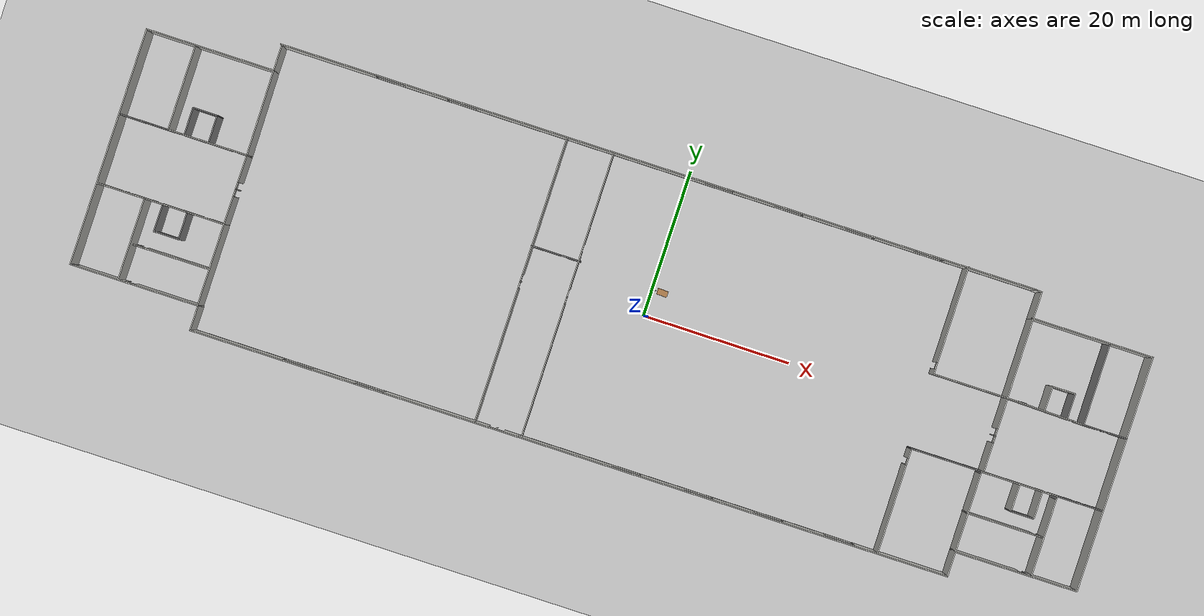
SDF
<sdf version="1.6">
 <world name="default">
  <light name="sun" type="directional">
   <pose>0 0 10 0 -0 0</pose>
   <diffuse>0.8 0.8 0.8 1</diffuse>
   <specular>0.1 0.1 0.1 1</specular>
   <attenuation>
    <range>1000</range>
    <constant>0.9</constant>
    <linear>0.01</linear>
    <quadratic>0.001</quadratic>
   </attenuation>
   <direction>-0.5 0.5 -1</direction>
  </light>
  <model name="ground_plane">
   <static>1</static>
   <link name="link">
    <collision name="collision">
     <geometry><plane><normal>0 0 1</normal><size>100 100</size></plane></geometry>
     <surface><friction><ode><mu>100</mu><mu2>50</mu2></ode></friction></surface>
    </collision>
    <visual name="visual">
     <cast_shadows>0</cast_shadows>
     <geometry><plane><normal>0 0 1</normal><size>100 100</size></plane></geometry>
     <material>
      <script><uri>file://media/materials/scripts/gazebo.material</uri><name>Gazebo/Grey</name></script>
     </material>
    </visual>
   </link>
  </model>
  <gravity>0 0 -9.8</gravity>
  <magnetic_field>6e-06 2.3e-05 -4.2e-05</magnetic_field>
  <atmosphere type="adiabatic"/>
  <physics name="default_physics" default="0" type="ode">
   <max_step_size>0.001</max_step_size>
   <real_time_factor>1</real_time_factor>
   <real_time_update_rate>1000</real_time_update_rate>
  </physics>
  <scene><ambient>0.4 0.4 0.4 1</ambient><background>0.7 0.7 0.7 1</background><shadows>1</shadows></scene>
  <spherical_coordinates>
   <surface_model>EARTH_WGS84</surface_model>
   <latitude_deg>0</latitude_deg>
   <longitude_deg>0</longitude_deg>
   <elevation>0</elevation>
   <heading_deg>0</heading_deg>
  </spherical_coordinates>
  <model name="Erdgeschossen_labor">
   <pose>-4.29246 -0.487524 0 0 -0 0</pose>
   <link name="Door_37">
    <collision name="Door_37_Collision">
     <geometry><box><size>0.9 0.17 2</size></box></geometry>
     <pose>0 0 1 0 -0 0</pose>
    </collision>
    <visual name="Door_37_Visual">
     <pose>0 0 1 0 -0 0</pose>
     <geometry><box><size>0.9 0.17 2</size></box></geometry>
     <material>
      <script><uri>file://media/materials/scripts/gazebo.material</uri><name>Gazebo/Grey</name></script>
     </material>
    </visual>
    <pose>54.7211 4.95557 0 0 -0 0</pose>
   </link>
   <link name="Wall_0">
    <pose>-0.038053 19.4617 0 0 -0 0</pose>
    <visual name="Wall_0_Visual_0">
     <pose>-45.1164 0 1.25 0 -0 0</pose>
     <geometry><box><size>13.0172 0.15 2.5</size></box></geometry>
     <material>
      <script><uri>file://media/materials/scripts/gazebo.material</uri><name>Gazebo/CeilingTiled</name></script>
      <ambient>1 1 1 1</ambient>
     </material>
    </visual>
    <collision name="Wall_0_Collision_0">
     <geometry><box><size>13.0172 0.15 2.5</size></box></geometry>
     <pose>-45.1164 0 1.25 0 -0 0</pose>
    </collision>
    <visual name="Wall_0_Visual_1">
     <pose>6.50859 0 0.1 0 -0 0</pose>
     <geometry><box><size>90.2328 0.15 0.2</size></box></geometry>
     <material>
      <script><uri>file://media/materials/scripts/gazebo.material</uri><name>Gazebo/CeilingTiled</name></script>
      <ambient>1 1 1 1</ambient>
     </material>
    </visual>
    <collision name="Wall_0_Collision_1">
     <geometry><box><size>90.2328 0.15 0.2</size></box></geometry>
     <pose>6.50859 0 0.1 0 -0 0</pose>
    </collision>
    <visual name="Wall_0_Visual_2">
     <pose>-31.7614 0 1.35 0 -0 0</pose>
     <geometry><box><size>5.93292 0.15 2.3</size></box></geometry>
     <material>
      <script><uri>file://media/materials/scripts/gazebo.material</uri><name>Gazebo/CeilingTiled</name></script>
      <ambient>1 1 1 1</ambient>
     </material>
    </visual>
    <collision name="Wall_0_Collision_2">
     <geometry><box><size>5.93292 0.15 2.3</size></box></geometry>
     <pose>-31.7614 0 1.35 0 -0 0</pose>
    </collision>
    <visual name="Wall_0_Visual_3">
     <pose>-9.24517 0 1.35 0 -0 0</pose>
     <geometry><box><size>31.3395 0.15 2.3</size></box></geometry>
     <material>
      <script><uri>file://media/materials/scripts/gazebo.material</uri><name>Gazebo/CeilingTiled</name></script>
      <ambient>1 1 1 1</ambient>
     </material>
    </visual>
    <collision name="Wall_0_Collision_3">
     <geometry><box><size>31.3395 0.15 2.3</size></box></geometry>
     <pose>-9.24517 0 1.35 0 -0 0</pose>
    </collision>
    <visual name="Wall_0_Visual_4">
     <pose>13.191 0 1.35 0 -0 0</pose>
     <geometry><box><size>5.77285 0.15 2.3</size></box></geometry>
     <material>
      <script><uri>file://media/materials/scripts/gazebo.material</uri><name>Gazebo/CeilingTiled</name></script>
      <ambient>1 1 1 1</ambient>
     </material>
    </visual>
    <collision name="Wall_0_Collision_4">
     <geometry><box><size>5.77285 0.15 2.3</size></box></geometry>
     <pose>13.191 0 1.35 0 -0 0</pose>
    </collision>
    <visual name="Wall_0_Visual_5">
     <pose>22.9057 0 1.35 0 -0 0</pose>
     <geometry><box><size>5.89661 0.15 2.3</size></box></geometry>
     <material>
      <script><uri>file://media/materials/scripts/gazebo.material</uri><name>Gazebo/CeilingTiled</name></script>
      <ambient>1 1 1 1</ambient>
     </material>
    </visual>
    <collision name="Wall_0_Collision_5">
     <geometry><box><size>5.89661 0.15 2.3</size></box></geometry>
     <pose>22.9057 0 1.35 0 -0 0</pose>
    </collision>
    <visual name="Wall_0_Visual_6">
     <pose>32.4967 0 1.35 0 -0 0</pose>
     <geometry><box><size>5.52534 0.15 2.3</size></box></geometry>
     <material>
      <script><uri>file://media/materials/scripts/gazebo.material</uri><name>Gazebo/CeilingTiled</name></script>
      <ambient>1 1 1 1</ambient>
     </material>
    </visual>
    <collision name="Wall_0_Collision_6">
     <geometry><box><size>5.52534 0.15 2.3</size></box></geometry>
     <pose>32.4967 0 1.35 0 -0 0</pose>
    </collision>
    <visual name="Wall_0_Visual_7">
     <pose>45.3822 0 1.35 0 -0 0</pose>
     <geometry><box><size>12.4856 0.15 2.3</size></box></geometry>
     <material>
      <script><uri>file://media/materials/scripts/gazebo.material</uri><name>Gazebo/CeilingTiled</name></script>
      <ambient>1 1 1 1</ambient>
     </material>
    </visual>
    <collision name="Wall_0_Collision_7">
     <geometry><box><size>12.4856 0.15 2.3</size></box></geometry>
     <pose>45.3822 0 1.35 0 -0 0</pose>
    </collision>
    <visual name="Wall_0_Visual_8">
     <pose>-36.6678 0 2.35 0 -0 0</pose>
     <geometry><box><size>3.88 0.15 0.3</size></box></geometry>
     <material>
      <script><uri>file://media/materials/scripts/gazebo.material</uri><name>Gazebo/CeilingTiled</name></script>
      <ambient>1 1 1 1</ambient>
     </material>
    </visual>
    <collision name="Wall_0_Collision_8">
     <geometry><box><size>3.88 0.15 0.3</size></box></geometry>
     <pose>-36.6678 0 2.35 0 -0 0</pose>
    </collision>
    <visual name="Wall_0_Visual_9">
     <pose>-26.8549 0 2.35 0 -0 0</pose>
     <geometry><box><size>3.88 0.15 0.3</size></box></geometry>
     <material>
      <script><uri>file://media/materials/scripts/gazebo.material</uri><name>Gazebo/CeilingTiled</name></script>
      <ambient>1 1 1 1</ambient>
     </material>
    </visual>
    <collision name="Wall_0_Collision_9">
     <geometry><box><size>3.88 0.15 0.3</size></box></geometry>
     <pose>-26.8549 0 2.35 0 -0 0</pose>
    </collision>
    <visual name="Wall_0_Visual_10">
     <pose>8.36458 0 2.35 0 -0 0</pose>
     <geometry><box><size>3.88 0.15 0.3</size></box></geometry>
     <material>
      <script><uri>file://media/materials/scripts/gazebo.material</uri><name>Gazebo/CeilingTiled</name></script>
      <ambient>1 1 1 1</ambient>
     </material>
    </visual>
    <collision name="Wall_0_Collision_10">
     <geometry><box><size>3.88 0.15 0.3</size></box></geometry>
     <pose>8.36458 0 2.35 0 -0 0</pose>
    </collision>
    <visual name="Wall_0_Visual_11">
     <pose>18.0174 0 2.35 0 -0 0</pose>
     <geometry><box><size>3.88 0.15 0.3</size></box></geometry>
     <material>
      <script><uri>file://media/materials/scripts/gazebo.material</uri><name>Gazebo/CeilingTiled</name></script>
      <ambient>1 1 1 1</ambient>
     </material>
    </visual>
    <collision name="Wall_0_Collision_11">
     <geometry><box><size>3.88 0.15 0.3</size></box></geometry>
     <pose>18.0174 0 2.35 0 -0 0</pose>
    </collision>
    <visual name="Wall_0_Visual_12">
     <pose>27.794 0 2.35 0 -0 0</pose>
     <geometry><box><size>3.88 0.15 0.3</size></box></geometry>
     <material>
      <script><uri>file://media/materials/scripts/gazebo.material</uri><name>Gazebo/CeilingTiled</name></script>
      <ambient>1 1 1 1</ambient>
     </material>
    </visual>
    <collision name="Wall_0_Collision_12">
     <geometry><box><size>3.88 0.15 0.3</size></box></geometry>
     <pose>27.794 0 2.35 0 -0 0</pose>
    </collision>
    <visual name="Wall_0_Visual_13">
     <pose>37.1994 0 2.35 0 -0 0</pose>
     <geometry><box><size>3.88 0.15 0.3</size></box></geometry>
     <material>
      <script><uri>file://media/materials/scripts/gazebo.material</uri><name>Gazebo/CeilingTiled</name></script>
      <ambient>1 1 1 1</ambient>
     </material>
    </visual>
    <collision name="Wall_0_Collision_13">
     <geometry><box><size>3.88 0.15 0.3</size></box></geometry>
     <pose>37.1994 0 2.35 0 -0 0</pose>
    </collision>
   </link>
   <link name="Wall_10">
    <pose>65.825 4.6812 0 0 -0 3.14159</pose>
    <visual name="Wall_10_Visual_0">
     <pose>-2.15466 0 1.25 0 -0 0</pose>
     <geometry><box><size>1.69069 0.15 2.5</size></box></geometry>
     <material>
      <script><uri>file://media/materials/scripts/gazebo.material</uri><name>Gazebo/Grey</name></script>
      <ambient>1 1 1 1</ambient>
     </material>
    </visual>
    <collision name="Wall_10_Collision_0">
     <geometry><box><size>1.69069 0.15 2.5</size></box></geometry>
     <pose>-2.15466 0 1.25 0 -0 0</pose>
    </collision>
    <visual name="Wall_10_Visual_1">
     <pose>-0.324451 0 1.25 0 -0 0</pose>
     <geometry><box><size>0.169725 0.15 2.5</size></box></geometry>
     <material>
      <script><uri>file://media/materials/scripts/gazebo.material</uri><name>Gazebo/Grey</name></script>
      <ambient>1 1 1 1</ambient>
     </material>
    </visual>
    <collision name="Wall_10_Collision_1">
     <geometry><box><size>0.169725 0.15 2.5</size></box></geometry>
     <pose>-0.324451 0 1.25 0 -0 0</pose>
    </collision>
    <visual name="Wall_10_Visual_2">
     <pose>1.83021 0 1.25 0 -0 0</pose>
     <geometry><box><size>2.33959 0.15 2.5</size></box></geometry>
     <material>
      <script><uri>file://media/materials/scripts/gazebo.material</uri><name>Gazebo/Grey</name></script>
      <ambient>1 1 1 1</ambient>
     </material>
    </visual>
    <collision name="Wall_10_Collision_2">
     <geometry><box><size>2.33959 0.15 2.5</size></box></geometry>
     <pose>1.83021 0 1.25 0 -0 0</pose>
    </collision>
    <visual name="Wall_10_Visual_3">
     <pose>-0.859314 0 2.25 0 -0 0</pose>
     <geometry><box><size>0.9 0.15 0.5</size></box></geometry>
     <material>
      <script><uri>file://media/materials/scripts/gazebo.material</uri><name>Gazebo/Grey</name></script>
      <ambient>1 1 1 1</ambient>
     </material>
    </visual>
    <collision name="Wall_10_Collision_3">
     <geometry><box><size>0.9 0.15 0.5</size></box></geometry>
     <pose>-0.859314 0 2.25 0 -0 0</pose>
    </collision>
    <visual name="Wall_10_Visual_4">
     <pose>0.210411 0 2.25 0 -0 0</pose>
     <geometry><box><size>0.9 0.15 0.5</size></box></geometry>
     <material>
      <script><uri>file://media/materials/scripts/gazebo.material</uri><name>Gazebo/Grey</name></script>
      <ambient>1 1 1 1</ambient>
     </material>
    </visual>
    <collision name="Wall_10_Collision_4">
     <geometry><box><size>0.9 0.15 0.5</size></box></geometry>
     <pose>0.210411 0 2.25 0 -0 0</pose>
    </collision>
   </link>
   <link name="Wall_11">
    <collision name="Wall_11_Collision">
     <geometry><box><size>11 0.15 2.5</size></box></geometry>
     <pose>0 0 1.25 0 -0 0</pose>
    </collision>
    <visual name="Wall_11_Visual">
     <pose>0 0 1.25 0 -0 0</pose>
     <geometry><box><size>11 0.15 2.5</size></box></geometry>
     <material>
      <script><uri>file://media/materials/scripts/gazebo.material</uri><name>Gazebo/Grey</name></script>
      <ambient>1 1 1 1</ambient>
     </material>
    </visual>
    <pose>62.9 10.1062 0 0 -0 1.5708</pose>
   </link>
   <link name="Wall_13">
    <collision name="Wall_13_Collision">
     <geometry><box><size>1.04169 0.15 2.5</size></box></geometry>
     <pose>0 0 1.25 0 -0 0</pose>
    </collision>
    <visual name="Wall_13_Visual">
     <pose>0 0 1.25 0 -0 0</pose>
     <geometry><box><size>1.04169 0.15 2.5</size></box></geometry>
     <material>
      <script><uri>file://media/materials/scripts/gazebo.material</uri><name>Gazebo/CeilingTiled</name></script>
      <ambient>1 1 1 1</ambient>
     </material>
    </visual>
    <pose>51.956 19.4215 0 0 -0 3.05118</pose>
   </link>
   <link name="Wall_15">
    <collision name="Wall_15_Collision">
     <geometry><box><size>11 0.15 2.5</size></box></geometry>
     <pose>0 0 1.25 0 -0 0</pose>
    </collision>
    <visual name="Wall_15_Visual">
     <pose>0 0 1.25 0 -0 0</pose>
     <geometry><box><size>11 0.15 2.5</size></box></geometry>
     <material>
      <script><uri>file://media/materials/scripts/gazebo.material</uri><name>Gazebo/CeilingTiled</name></script>
      <ambient>1 1 1 1</ambient>
     </material>
    </visual>
    <pose>52.4 10.3562 0 0 0 -1.5708</pose>
   </link>
   <link name="Wall_16">
    <pose>57.65 4.8062 0 0 0 -0.023805</pose>
    <visual name="Wall_16_Visual_0">
     <pose>-0.791437 0 1.25 0 -0 0</pose>
     <geometry><box><size>9.0701 0.15 2.5</size></box></geometry>
     <material>
      <script><uri>file://media/materials/scripts/gazebo.material</uri><name>Gazebo/CeilingTiled</name></script>
      <ambient>1 1 1 1</ambient>
     </material>
    </visual>
    <collision name="Wall_16_Collision_0">
     <geometry><box><size>9.0701 0.15 2.5</size></box></geometry>
     <pose>-0.791437 0 1.25 0 -0 0</pose>
    </collision>
    <visual name="Wall_16_Visual_1">
     <pose>4.98505 0 1.25 0 -0 0</pose>
     <geometry><box><size>0.682875 0.15 2.5</size></box></geometry>
     <material>
      <script><uri>file://media/materials/scripts/gazebo.material</uri><name>Gazebo/CeilingTiled</name></script>
      <ambient>1 1 1 1</ambient>
     </material>
    </visual>
    <collision name="Wall_16_Collision_1">
     <geometry><box><size>0.682875 0.15 2.5</size></box></geometry>
     <pose>4.98505 0 1.25 0 -0 0</pose>
    </collision>
    <visual name="Wall_16_Visual_2">
     <pose>4.19361 0 2.25 0 -0 0</pose>
     <geometry><box><size>0.9 0.15 0.5</size></box></geometry>
     <material>
      <script><uri>file://media/materials/scripts/gazebo.material</uri><name>Gazebo/CeilingTiled</name></script>
      <ambient>1 1 1 1</ambient>
     </material>
    </visual>
    <collision name="Wall_16_Collision_2">
     <geometry><box><size>0.9 0.15 0.5</size></box></geometry>
     <pose>4.19361 0 2.25 0 -0 0</pose>
    </collision>
   </link>
   <link name="Wall_18">
    <collision name="Wall_18_Collision">
     <geometry><box><size>21 0.15 2.5</size></box></geometry>
     <pose>0 0 1.25 0 -0 0</pose>
    </collision>
    <visual name="Wall_18_Visual">
     <pose>0 0 1.25 0 -0 0</pose>
     <geometry><box><size>21 0.15 2.5</size></box></geometry>
     <material>
      <script><uri>file://media/materials/scripts/gazebo.material</uri><name>Gazebo/CeilingTiled</name></script>
      <ambient>1 1 1 1</ambient>
     </material>
    </visual>
    <pose>68.75 -5.7438 0 0 0 -1.5708</pose>
   </link>
   <link name="Wall_19">
    <pose>60.45 -16.1688 0 0 -0 3.14159</pose>
    <visual name="Wall_19_Visual_0">
     <pose>-4.96727 0 1.25 0 -0 0</pose>
     <geometry><box><size>6.81547 0.15 2.5</size></box></geometry>
     <material>
      <script><uri>file://media/materials/scripts/gazebo.material</uri><name>Gazebo/CeilingTiled</name></script>
      <ambient>1 1 1 1</ambient>
     </material>
    </visual>
    <collision name="Wall_19_Collision_0">
     <geometry><box><size>6.81547 0.15 2.5</size></box></geometry>
     <pose>-4.96727 0 1.25 0 -0 0</pose>
    </collision>
    <visual name="Wall_19_Visual_1">
     <pose>3.85773 0 1.25 0 -0 0</pose>
     <geometry><box><size>9.03453 0.15 2.5</size></box></geometry>
     <material>
      <script><uri>file://media/materials/scripts/gazebo.material</uri><name>Gazebo/CeilingTiled</name></script>
      <ambient>1 1 1 1</ambient>
     </material>
    </visual>
    <collision name="Wall_19_Collision_1">
     <geometry><box><size>9.03453 0.15 2.5</size></box></geometry>
     <pose>3.85773 0 1.25 0 -0 0</pose>
    </collision>
    <visual name="Wall_19_Visual_2">
     <pose>-1.10953 0 2.25 0 -0 0</pose>
     <geometry><box><size>0.9 0.15 0.5</size></box></geometry>
     <material>
      <script><uri>file://media/materials/scripts/gazebo.material</uri><name>Gazebo/CeilingTiled</name></script>
      <ambient>1 1 1 1</ambient>
     </material>
    </visual>
    <collision name="Wall_19_Collision_2">
     <geometry><box><size>0.9 0.15 0.5</size></box></geometry>
     <pose>-1.10953 0 2.25 0 -0 0</pose>
    </collision>
   </link>
   <link name="Wall_20">
    <collision name="Wall_20_Collision">
     <geometry><box><size>10.75 0.15 2.5</size></box></geometry>
     <pose>0 0 1.25 0 -0 0</pose>
    </collision>
    <visual name="Wall_20_Visual">
     <pose>0 0 1.25 0 -0 0</pose>
     <geometry><box><size>10.75 0.15 2.5</size></box></geometry>
     <material>
      <script><uri>file://media/materials/scripts/gazebo.material</uri><name>Gazebo/CeilingTiled</name></script>
      <ambient>1 1 1 1</ambient>
     </material>
    </visual>
    <pose>52.15 -10.8688 0 0 -0 1.5708</pose>
   </link>
   <link name="Wall_22">
    <collision name="Wall_22_Collision">
     <geometry><box><size>10.5 0.15 2.5</size></box></geometry>
     <pose>0 0 1.25 0 -0 0</pose>
    </collision>
    <visual name="Wall_22_Visual">
     <pose>0 0 1.25 0 -0 0</pose>
     <geometry><box><size>10.5 0.15 2.5</size></box></geometry>
     <material>
      <script><uri>file://media/materials/scripts/gazebo.material</uri><name>Gazebo/CeilingTiled</name></script>
      <ambient>1 1 1 1</ambient>
     </material>
    </visual>
    <pose>62.5 -10.7438 0 0 0 -1.5708</pose>
   </link>
   <link name="Wall_25">
    <collision name="Wall_25_Collision">
     <geometry><box><size>0.5 0.15 2.5</size></box></geometry>
     <pose>0 0 1.25 0 -0 0</pose>
    </collision>
    <visual name="Wall_25_Visual">
     <pose>0 0 1.25 0 -0 0</pose>
     <geometry><box><size>0.5 0.15 2.5</size></box></geometry>
     <material>
      <script><uri>file://media/materials/scripts/gazebo.material</uri><name>Gazebo/Grey</name></script>
      <ambient>1 1 1 1</ambient>
     </material>
    </visual>
    <pose>52.15 -5.3938 0 0 -0 1.5708</pose>
   </link>
   <link name="Wall_26">
    <pose>57.325 -5.2188 0 0 -0 0</pose>
    <visual name="Wall_26_Visual_0">
     <pose>-0.710538 0 1.25 0 -0 0</pose>
     <geometry><box><size>9.07892 0.15 2.5</size></box></geometry>
     <material>
      <script><uri>file://media/materials/scripts/gazebo.material</uri><name>Gazebo/CeilingTiled</name></script>
      <ambient>1 1 1 1</ambient>
     </material>
    </visual>
    <collision name="Wall_26_Collision_0">
     <geometry><box><size>9.07892 0.15 2.5</size></box></geometry>
     <pose>-0.710538 0 1.25 0 -0 0</pose>
    </collision>
    <visual name="Wall_26_Visual_1">
     <pose>4.98946 0 1.25 0 -0 0</pose>
     <geometry><box><size>0.521077 0.15 2.5</size></box></geometry>
     <material>
      <script><uri>file://media/materials/scripts/gazebo.material</uri><name>Gazebo/CeilingTiled</name></script>
      <ambient>1 1 1 1</ambient>
     </material>
    </visual>
    <collision name="Wall_26_Collision_1">
     <geometry><box><size>0.521077 0.15 2.5</size></box></geometry>
     <pose>4.98946 0 1.25 0 -0 0</pose>
    </collision>
    <visual name="Wall_26_Visual_2">
     <pose>4.27892 0 2.25 0 -0 0</pose>
     <geometry><box><size>0.9 0.15 0.5</size></box></geometry>
     <material>
      <script><uri>file://media/materials/scripts/gazebo.material</uri><name>Gazebo/CeilingTiled</name></script>
      <ambient>1 1 1 1</ambient>
     </material>
    </visual>
    <collision name="Wall_26_Collision_2">
     <geometry><box><size>0.9 0.15 0.5</size></box></geometry>
     <pose>4.27892 0 2.25 0 -0 0</pose>
    </collision>
   </link>
   <link name="Wall_27">
    <collision name="Wall_27_Collision">
     <geometry><box><size>0.5 0.15 2.5</size></box></geometry>
     <pose>0 0 1.25 0 -0 0</pose>
    </collision>
    <visual name="Wall_27_Visual">
     <pose>0 0 1.25 0 -0 0</pose>
     <geometry><box><size>0.5 0.15 2.5</size></box></geometry>
     <material>
      <script><uri>file://media/materials/scripts/gazebo.material</uri><name>Gazebo/Grey</name></script>
      <ambient>1 1 1 1</ambient>
     </material>
    </visual>
    <pose>62.5 -5.3938 0 0 0 -1.5708</pose>
   </link>
   <link name="Wall_29">
    <pose>65.55 -5.2188 0 0 -0 0</pose>
    <visual name="Wall_29_Visual_0">
     <pose>-1.74988 0 1.25 0 -0 0</pose>
     <geometry><box><size>2.75023 0.15 2.5</size></box></geometry>
     <material>
      <script><uri>file://media/materials/scripts/gazebo.material</uri><name>Gazebo/Grey</name></script>
      <ambient>1 1 1 1</ambient>
     </material>
    </visual>
    <collision name="Wall_29_Collision_0">
     <geometry><box><size>2.75023 0.15 2.5</size></box></geometry>
     <pose>-1.74988 0 1.25 0 -0 0</pose>
    </collision>
    <visual name="Wall_29_Visual_1">
     <pose>0.607143 0 1.25 0 -0 0</pose>
     <geometry><box><size>0.16382 0.15 2.5</size></box></geometry>
     <material>
      <script><uri>file://media/materials/scripts/gazebo.material</uri><name>Gazebo/Grey</name></script>
      <ambient>1 1 1 1</ambient>
     </material>
    </visual>
    <collision name="Wall_29_Collision_1">
     <geometry><box><size>0.16382 0.15 2.5</size></box></geometry>
     <pose>0.607143 0 1.25 0 -0 0</pose>
    </collision>
    <visual name="Wall_29_Visual_2">
     <pose>2.35703 0 1.25 0 -0 0</pose>
     <geometry><box><size>1.53595 0.15 2.5</size></box></geometry>
     <material>
      <script><uri>file://media/materials/scripts/gazebo.material</uri><name>Gazebo/Grey</name></script>
      <ambient>1 1 1 1</ambient>
     </material>
    </visual>
    <collision name="Wall_29_Collision_2">
     <geometry><box><size>1.53595 0.15 2.5</size></box></geometry>
     <pose>2.35703 0 1.25 0 -0 0</pose>
    </collision>
    <visual name="Wall_29_Visual_3">
     <pose>0.075233 0 2.25 0 -0 0</pose>
     <geometry><box><size>0.9 0.15 0.5</size></box></geometry>
     <material>
      <script><uri>file://media/materials/scripts/gazebo.material</uri><name>Gazebo/Grey</name></script>
      <ambient>1 1 1 1</ambient>
     </material>
    </visual>
    <collision name="Wall_29_Collision_3">
     <geometry><box><size>0.9 0.15 0.5</size></box></geometry>
     <pose>0.075233 0 2.25 0 -0 0</pose>
    </collision>
    <visual name="Wall_29_Visual_4">
     <pose>1.13905 0 2.25 0 -0 0</pose>
     <geometry><box><size>0.9 0.15 0.5</size></box></geometry>
     <material>
      <script><uri>file://media/materials/scripts/gazebo.material</uri><name>Gazebo/Grey</name></script>
      <ambient>1 1 1 1</ambient>
     </material>
    </visual>
    <collision name="Wall_29_Collision_4">
     <geometry><box><size>0.9 0.15 0.5</size></box></geometry>
     <pose>1.13905 0 2.25 0 -0 0</pose>
    </collision>
   </link>
   <link name="Wall_31">
    <collision name="Wall_31_Collision">
     <geometry><box><size>3.5 0.15 2.5</size></box></geometry>
     <pose>0 0 1.25 0 -0 0</pose>
    </collision>
    <visual name="Wall_31_Visual">
     <pose>0 0 1.25 0 -0 0</pose>
     <geometry><box><size>3.5 0.15 2.5</size></box></geometry>
     <material>
      <script><uri>file://media/materials/scripts/gazebo.material</uri><name>Gazebo/CeilingTiled</name></script>
      <ambient>1 1 1 1</ambient>
     </material>
    </visual>
    <pose>52.15 -17.8438 0 0 0 -1.5708</pose>
   </link>
   <link name="Wall_32">
    <pose>22.85 -19.5188 0 0 -0 3.14159</pose>
    <visual name="Wall_32_Visual_0">
     <pose>-22.984 0 1.25 0 -0 0</pose>
     <geometry><box><size>12.7819 0.15 2.5</size></box></geometry>
     <material>
      <script><uri>file://media/materials/scripts/gazebo.material</uri><name>Gazebo/CeilingTiled</name></script>
      <ambient>1 1 1 1</ambient>
     </material>
    </visual>
    <collision name="Wall_32_Collision_0">
     <geometry><box><size>12.7819 0.15 2.5</size></box></geometry>
     <pose>-22.984 0 1.25 0 -0 0</pose>
    </collision>
    <visual name="Wall_32_Visual_1">
     <pose>6.39096 0 0.1 0 -0 0</pose>
     <geometry><box><size>45.9681 0.15 0.2</size></box></geometry>
     <material>
      <script><uri>file://media/materials/scripts/gazebo.material</uri><name>Gazebo/CeilingTiled</name></script>
      <ambient>1 1 1 1</ambient>
     </material>
    </visual>
    <collision name="Wall_32_Collision_1">
     <geometry><box><size>45.9681 0.15 0.2</size></box></geometry>
     <pose>6.39096 0 0.1 0 -0 0</pose>
    </collision>
    <visual name="Wall_32_Visual_2">
     <pose>-9.79822 0 1.35 0 -0 0</pose>
     <geometry><box><size>5.82974 0.15 2.3</size></box></geometry>
     <material>
      <script><uri>file://media/materials/scripts/gazebo.material</uri><name>Gazebo/CeilingTiled</name></script>
      <ambient>1 1 1 1</ambient>
     </material>
    </visual>
    <collision name="Wall_32_Collision_2">
     <geometry><box><size>5.82974 0.15 2.3</size></box></geometry>
     <pose>-9.79822 0 1.35 0 -0 0</pose>
    </collision>
    <visual name="Wall_32_Visual_3">
     <pose>-0.149557 0 1.35 0 -0 0</pose>
     <geometry><box><size>5.70758 0.15 2.3</size></box></geometry>
     <material>
      <script><uri>file://media/materials/scripts/gazebo.material</uri><name>Gazebo/CeilingTiled</name></script>
      <ambient>1 1 1 1</ambient>
     </material>
    </visual>
    <collision name="Wall_32_Collision_3">
     <geometry><box><size>5.70758 0.15 2.3</size></box></geometry>
     <pose>-0.149557 0 1.35 0 -0 0</pose>
    </collision>
    <visual name="Wall_32_Visual_4">
     <pose>9.60231 0 1.35 0 -0 0</pose>
     <geometry><box><size>6.03615 0.15 2.3</size></box></geometry>
     <material>
      <script><uri>file://media/materials/scripts/gazebo.material</uri><name>Gazebo/CeilingTiled</name></script>
      <ambient>1 1 1 1</ambient>
     </material>
    </visual>
    <collision name="Wall_32_Collision_4">
     <geometry><box><size>6.03615 0.15 2.3</size></box></geometry>
     <pose>9.60231 0 1.35 0 -0 0</pose>
    </collision>
    <visual name="Wall_32_Visual_5">
     <pose>22.9377 0 1.35 0 -0 0</pose>
     <geometry><box><size>12.8746 0.15 2.3</size></box></geometry>
     <material>
      <script><uri>file://media/materials/scripts/gazebo.material</uri><name>Gazebo/CeilingTiled</name></script>
      <ambient>1 1 1 1</ambient>
     </material>
    </visual>
    <collision name="Wall_32_Collision_5">
     <geometry><box><size>12.8746 0.15 2.3</size></box></geometry>
     <pose>22.9377 0 1.35 0 -0 0</pose>
    </collision>
    <visual name="Wall_32_Visual_6">
     <pose>-14.6531 0 2.35 0 -0 0</pose>
     <geometry><box><size>3.88 0.15 0.3</size></box></geometry>
     <material>
      <script><uri>file://media/materials/scripts/gazebo.material</uri><name>Gazebo/CeilingTiled</name></script>
      <ambient>1 1 1 1</ambient>
     </material>
    </visual>
    <collision name="Wall_32_Collision_6">
     <geometry><box><size>3.88 0.15 0.3</size></box></geometry>
     <pose>-14.6531 0 2.35 0 -0 0</pose>
    </collision>
    <visual name="Wall_32_Visual_7">
     <pose>-4.94335 0 2.35 0 -0 0</pose>
     <geometry><box><size>3.88 0.15 0.3</size></box></geometry>
     <material>
      <script><uri>file://media/materials/scripts/gazebo.material</uri><name>Gazebo/CeilingTiled</name></script>
      <ambient>1 1 1 1</ambient>
     </material>
    </visual>
    <collision name="Wall_32_Collision_7">
     <geometry><box><size>3.88 0.15 0.3</size></box></geometry>
     <pose>-4.94335 0 2.35 0 -0 0</pose>
    </collision>
    <visual name="Wall_32_Visual_8">
     <pose>4.64423 0 2.35 0 -0 0</pose>
     <geometry><box><size>3.88 0.15 0.3</size></box></geometry>
     <material>
      <script><uri>file://media/materials/scripts/gazebo.material</uri><name>Gazebo/CeilingTiled</name></script>
      <ambient>1 1 1 1</ambient>
     </material>
    </visual>
    <collision name="Wall_32_Collision_8">
     <geometry><box><size>3.88 0.15 0.3</size></box></geometry>
     <pose>4.64423 0 2.35 0 -0 0</pose>
    </collision>
    <visual name="Wall_32_Visual_9">
     <pose>14.5604 0 2.35 0 -0 0</pose>
     <geometry><box><size>3.88 0.15 0.3</size></box></geometry>
     <material>
      <script><uri>file://media/materials/scripts/gazebo.material</uri><name>Gazebo/CeilingTiled</name></script>
      <ambient>1 1 1 1</ambient>
     </material>
    </visual>
    <collision name="Wall_32_Collision_9">
     <geometry><box><size>3.88 0.15 0.3</size></box></geometry>
     <pose>14.5604 0 2.35 0 -0 0</pose>
    </collision>
   </link>
   <link name="Wall_34">
    <pose>-28.875 -19.5188 0 0 -0 3.14159</pose>
    <visual name="Wall_34_Visual_0">
     <pose>-21.4228 0 1.25 0 -0 0</pose>
     <geometry><box><size>2.1544 0.15 2.5</size></box></geometry>
     <material>
      <script><uri>file://media/materials/scripts/gazebo.material</uri><name>Gazebo/CeilingTiled</name></script>
      <ambient>1 1 1 1</ambient>
     </material>
    </visual>
    <collision name="Wall_34_Collision_0">
     <geometry><box><size>2.1544 0.15 2.5</size></box></geometry>
     <pose>-21.4228 0 1.25 0 -0 0</pose>
    </collision>
    <visual name="Wall_34_Visual_1">
     <pose>-19.364 0 1.25 0 -0 0</pose>
     <geometry><box><size>0.163249 0.15 2.5</size></box></geometry>
     <material>
      <script><uri>file://media/materials/scripts/gazebo.material</uri><name>Gazebo/CeilingTiled</name></script>
      <ambient>1 1 1 1</ambient>
     </material>
    </visual>
    <collision name="Wall_34_Collision_1">
     <geometry><box><size>0.163249 0.15 2.5</size></box></geometry>
     <pose>-19.364 0 1.25 0 -0 0</pose>
    </collision>
    <visual name="Wall_34_Visual_2">
     <pose>-11.1612 0 1.25 0 -0 0</pose>
     <geometry><box><size>14.4423 0.15 2.5</size></box></geometry>
     <material>
      <script><uri>file://media/materials/scripts/gazebo.material</uri><name>Gazebo/CeilingTiled</name></script>
      <ambient>1 1 1 1</ambient>
     </material>
    </visual>
    <collision name="Wall_34_Collision_2">
     <geometry><box><size>14.4423 0.15 2.5</size></box></geometry>
     <pose>-11.1612 0 1.25 0 -0 0</pose>
    </collision>
    <visual name="Wall_34_Visual_3">
     <pose>9.27999 0 0.1 0 -0 0</pose>
     <geometry><box><size>26.44 0.15 0.2</size></box></geometry>
     <material>
      <script><uri>file://media/materials/scripts/gazebo.material</uri><name>Gazebo/CeilingTiled</name></script>
      <ambient>1 1 1 1</ambient>
     </material>
    </visual>
    <collision name="Wall_34_Collision_3">
     <geometry><box><size>26.44 0.15 0.2</size></box></geometry>
     <pose>9.27999 0 0.1 0 -0 0</pose>
    </collision>
    <visual name="Wall_34_Visual_4">
     <pose>2.95951 0 1.35 0 -0 0</pose>
     <geometry><box><size>6.03908 0.15 2.3</size></box></geometry>
     <material>
      <script><uri>file://media/materials/scripts/gazebo.material</uri><name>Gazebo/CeilingTiled</name></script>
      <ambient>1 1 1 1</ambient>
     </material>
    </visual>
    <collision name="Wall_34_Collision_4">
     <geometry><box><size>6.03908 0.15 2.3</size></box></geometry>
     <pose>2.95951 0 1.35 0 -0 0</pose>
    </collision>
    <visual name="Wall_34_Visual_5">
     <pose>16.1795 0 1.35 0 -0 0</pose>
     <geometry><box><size>12.641 0.15 2.3</size></box></geometry>
     <material>
      <script><uri>file://media/materials/scripts/gazebo.material</uri><name>Gazebo/CeilingTiled</name></script>
      <ambient>1 1 1 1</ambient>
     </material>
    </visual>
    <collision name="Wall_34_Collision_5">
     <geometry><box><size>12.641 0.15 2.3</size></box></geometry>
     <pose>16.1795 0 1.35 0 -0 0</pose>
    </collision>
    <visual name="Wall_34_Visual_6">
     <pose>-19.8956 0 2.25 0 -0 0</pose>
     <geometry><box><size>0.9 0.15 0.5</size></box></geometry>
     <material>
      <script><uri>file://media/materials/scripts/gazebo.material</uri><name>Gazebo/CeilingTiled</name></script>
      <ambient>1 1 1 1</ambient>
     </material>
    </visual>
    <collision name="Wall_34_Collision_6">
     <geometry><box><size>0.9 0.15 0.5</size></box></geometry>
     <pose>-19.8956 0 2.25 0 -0 0</pose>
    </collision>
    <visual name="Wall_34_Visual_7">
     <pose>-18.8323 0 2.25 0 -0 0</pose>
     <geometry><box><size>0.9 0.15 0.5</size></box></geometry>
     <material>
      <script><uri>file://media/materials/scripts/gazebo.material</uri><name>Gazebo/CeilingTiled</name></script>
      <ambient>1 1 1 1</ambient>
     </material>
    </visual>
    <collision name="Wall_34_Collision_7">
     <geometry><box><size>0.9 0.15 0.5</size></box></geometry>
     <pose>-18.8323 0 2.25 0 -0 0</pose>
    </collision>
    <visual name="Wall_34_Visual_8">
     <pose>-2.00003 0 2.35 0 -0 0</pose>
     <geometry><box><size>3.88 0.15 0.3</size></box></geometry>
     <material>
      <script><uri>file://media/materials/scripts/gazebo.material</uri><name>Gazebo/CeilingTiled</name></script>
      <ambient>1 1 1 1</ambient>
     </material>
    </visual>
    <collision name="Wall_34_Collision_8">
     <geometry><box><size>3.88 0.15 0.3</size></box></geometry>
     <pose>-2.00003 0 2.35 0 -0 0</pose>
    </collision>
    <visual name="Wall_34_Visual_9">
     <pose>7.91905 0 2.35 0 -0 0</pose>
     <geometry><box><size>3.88 0.15 0.3</size></box></geometry>
     <material>
      <script><uri>file://media/materials/scripts/gazebo.material</uri><name>Gazebo/CeilingTiled</name></script>
      <ambient>1 1 1 1</ambient>
     </material>
    </visual>
    <collision name="Wall_34_Collision_9">
     <geometry><box><size>3.88 0.15 0.3</size></box></geometry>
     <pose>7.91905 0 2.35 0 -0 0</pose>
    </collision>
   </link>
   <link name="Wall_35">
    <collision name="Wall_35_Collision">
     <geometry><box><size>3.5 0.15 2.5</size></box></geometry>
     <pose>0 0 1.25 0 -0 0</pose>
    </collision>
    <visual name="Wall_35_Visual">
     <pose>0 0 1.25 0 -0 0</pose>
     <geometry><box><size>3.5 0.15 2.5</size></box></geometry>
     <material>
      <script><uri>file://media/materials/scripts/gazebo.material</uri><name>Gazebo/CeilingTiled</name></script>
      <ambient>1 1 1 1</ambient>
     </material>
    </visual>
    <pose>-51.3 -17.8438 0 0 -0 1.5708</pose>
   </link>
   <link name="Wall_36">
    <pose>-59.725 -16.1688 0 0 -0 3.14159</pose>
    <visual name="Wall_36_Visual_0">
     <pose>-3.88185 0 1.25 0 -0 0</pose>
     <geometry><box><size>9.23631 0.15 2.5</size></box></geometry>
     <material>
      <script><uri>file://media/materials/scripts/gazebo.material</uri><name>Gazebo/CeilingTiled</name></script>
      <ambient>1 1 1 1</ambient>
     </material>
    </visual>
    <collision name="Wall_36_Collision_0">
     <geometry><box><size>9.23631 0.15 2.5</size></box></geometry>
     <pose>-3.88185 0 1.25 0 -0 0</pose>
    </collision>
    <visual name="Wall_36_Visual_1">
     <pose>5.06815 0 1.25 0 -0 0</pose>
     <geometry><box><size>6.86369 0.15 2.5</size></box></geometry>
     <material>
      <script><uri>file://media/materials/scripts/gazebo.material</uri><name>Gazebo/CeilingTiled</name></script>
      <ambient>1 1 1 1</ambient>
     </material>
    </visual>
    <collision name="Wall_36_Collision_1">
     <geometry><box><size>6.86369 0.15 2.5</size></box></geometry>
     <pose>5.06815 0 1.25 0 -0 0</pose>
    </collision>
    <visual name="Wall_36_Visual_2">
     <pose>1.18631 0 2.25 0 -0 0</pose>
     <geometry><box><size>0.9 0.15 0.5</size></box></geometry>
     <material>
      <script><uri>file://media/materials/scripts/gazebo.material</uri><name>Gazebo/CeilingTiled</name></script>
      <ambient>1 1 1 1</ambient>
     </material>
    </visual>
    <collision name="Wall_36_Collision_2">
     <geometry><box><size>0.9 0.15 0.5</size></box></geometry>
     <pose>1.18631 0 2.25 0 -0 0</pose>
    </collision>
   </link>
   <link name="Wall_38">
    <collision name="Wall_38_Collision">
     <geometry><box><size>0.75 0.15 2.5</size></box></geometry>
     <pose>0 0 1.25 0 -0 0</pose>
    </collision>
    <visual name="Wall_38_Visual">
     <pose>0 0 1.25 0 -0 0</pose>
     <geometry><box><size>0.75 0.15 2.5</size></box></geometry>
     <material>
      <script><uri>file://media/materials/scripts/gazebo.material</uri><name>Gazebo/Grey</name></script>
      <ambient>1 1 1 1</ambient>
     </material>
    </visual>
    <pose>-68.45 -16.1688 0 0 -0 3.14159</pose>
   </link>
   <link name="Wall_39">
    <collision name="Wall_39_Collision">
     <geometry><box><size>32.25 0.15 2.5</size></box></geometry>
     <pose>0 0 1.25 0 -0 0</pose>
    </collision>
    <visual name="Wall_39_Visual">
     <pose>0 0 1.25 0 -0 0</pose>
     <geometry><box><size>32.25 0.15 2.5</size></box></geometry>
     <material>
      <script><uri>file://media/materials/scripts/gazebo.material</uri><name>Gazebo/CeilingTiled</name></script>
      <ambient>1 1 1 1</ambient>
     </material>
    </visual>
    <pose>-68.75 -0.118799 0 0 -0 1.5708</pose>
   </link>
   <link name="Wall_40">
    <collision name="Wall_40_Collision">
     <geometry><box><size>17.5 0.15 2.5</size></box></geometry>
     <pose>0 0 1.25 0 -0 0</pose>
    </collision>
    <visual name="Wall_40_Visual">
     <pose>0 0 1.25 0 -0 0</pose>
     <geometry><box><size>17.5 0.15 2.5</size></box></geometry>
     <material>
      <script><uri>file://media/materials/scripts/gazebo.material</uri><name>Gazebo/CeilingTiled</name></script>
      <ambient>1 1 1 1</ambient>
     </material>
    </visual>
    <pose>-60.075 15.9312 0 0 -0 0</pose>
   </link>
   <link name="Wall_41">
    <collision name="Wall_41_Collision">
     <geometry><box><size>3.5 0.15 2.5</size></box></geometry>
     <pose>0 0 1.25 0 -0 0</pose>
    </collision>
    <visual name="Wall_41_Visual">
     <pose>0 0 1.25 0 -0 0</pose>
     <geometry><box><size>3.5 0.15 2.5</size></box></geometry>
     <material>
      <script><uri>file://media/materials/scripts/gazebo.material</uri><name>Gazebo/CeilingTiled</name></script>
      <ambient>1 1 1 1</ambient>
     </material>
    </visual>
    <pose>-51.4 17.6062 0 0 -0 1.5708</pose>
   </link>
   <link name="Wall_43">
    <collision name="Wall_43_Collision">
     <geometry><box><size>11.5 0.15 2.5</size></box></geometry>
     <pose>0 0 1.25 0 -0 0</pose>
    </collision>
    <visual name="Wall_43_Visual">
     <pose>0 0 1.25 0 -0 0</pose>
     <geometry><box><size>11.5 0.15 2.5</size></box></geometry>
     <material>
      <script><uri>file://media/materials/scripts/gazebo.material</uri><name>Gazebo/CeilingTiled</name></script>
      <ambient>1 1 1 1</ambient>
     </material>
    </visual>
    <pose>-62.0601 10.0639 0 0 0 -1.5708</pose>
   </link>
   <link name="Wall_44">
    <collision name="Wall_44_Collision">
     <geometry><box><size>6.75 0.15 2.5</size></box></geometry>
     <pose>0 0 1.25 0 -0 0</pose>
    </collision>
    <visual name="Wall_44_Visual">
     <pose>0 0 1.25 0 -0 0</pose>
     <geometry><box><size>6.75 0.15 2.5</size></box></geometry>
     <material>
      <script><uri>file://media/materials/scripts/gazebo.material</uri><name>Gazebo/Grey</name></script>
      <ambient>1 1 1 1</ambient>
     </material>
    </visual>
    <pose>-65.3601 4.3889 0 0 -0 3.14159</pose>
   </link>
   <link name="Wall_45">
    <pose>-59.9851 4.3889 0 0 -0 0</pose>
    <visual name="Wall_45_Visual_0">
     <pose>-7.39536 0 1.25 0 -0 0</pose>
     <geometry><box><size>2.70929 0.15 2.5</size></box></geometry>
     <material>
      <script><uri>file://media/materials/scripts/gazebo.material</uri><name>Gazebo/CeilingTiled</name></script>
      <ambient>1 1 1 1</ambient>
     </material>
    </visual>
    <collision name="Wall_45_Collision_0">
     <geometry><box><size>2.70929 0.15 2.5</size></box></geometry>
     <pose>-7.39536 0 1.25 0 -0 0</pose>
    </collision>
    <visual name="Wall_45_Visual_1">
     <pose>-5.0588 0 1.25 0 -0 0</pose>
     <geometry><box><size>0.163828 0.15 2.5</size></box></geometry>
     <material>
      <script><uri>file://media/materials/scripts/gazebo.material</uri><name>Gazebo/CeilingTiled</name></script>
      <ambient>1 1 1 1</ambient>
     </material>
    </visual>
    <collision name="Wall_45_Collision_1">
     <geometry><box><size>0.163828 0.15 2.5</size></box></geometry>
     <pose>-5.0588 0 1.25 0 -0 0</pose>
    </collision>
    <visual name="Wall_45_Visual_2">
     <pose>-2.64376 0 1.25 0 -0 0</pose>
     <geometry><box><size>2.86626 0.15 2.5</size></box></geometry>
     <material>
      <script><uri>file://media/materials/scripts/gazebo.material</uri><name>Gazebo/CeilingTiled</name></script>
      <ambient>1 1 1 1</ambient>
     </material>
    </visual>
    <collision name="Wall_45_Collision_2">
     <geometry><box><size>2.86626 0.15 2.5</size></box></geometry>
     <pose>-2.64376 0 1.25 0 -0 0</pose>
    </collision>
    <visual name="Wall_45_Visual_3">
     <pose>2.86545 0 1.25 0 -0 0</pose>
     <geometry><box><size>6.35215 0.15 2.5</size></box></geometry>
     <material>
      <script><uri>file://media/materials/scripts/gazebo.material</uri><name>Gazebo/CeilingTiled</name></script>
      <ambient>1 1 1 1</ambient>
     </material>
    </visual>
    <collision name="Wall_45_Collision_3">
     <geometry><box><size>6.35215 0.15 2.5</size></box></geometry>
     <pose>2.86545 0 1.25 0 -0 0</pose>
    </collision>
    <visual name="Wall_45_Visual_4">
     <pose>7.84576 0 1.25 0 -0 0</pose>
     <geometry><box><size>1.80847 0.15 2.5</size></box></geometry>
     <material>
      <script><uri>file://media/materials/scripts/gazebo.material</uri><name>Gazebo/CeilingTiled</name></script>
      <ambient>1 1 1 1</ambient>
     </material>
    </visual>
    <collision name="Wall_45_Collision_4">
     <geometry><box><size>1.80847 0.15 2.5</size></box></geometry>
     <pose>7.84576 0 1.25 0 -0 0</pose>
    </collision>
    <visual name="Wall_45_Visual_5">
     <pose>-5.59071 0 2.25 0 -0 0</pose>
     <geometry><box><size>0.9 0.15 0.5</size></box></geometry>
     <material>
      <script><uri>file://media/materials/scripts/gazebo.material</uri><name>Gazebo/CeilingTiled</name></script>
      <ambient>1 1 1 1</ambient>
     </material>
    </visual>
    <collision name="Wall_45_Collision_5">
     <geometry><box><size>0.9 0.15 0.5</size></box></geometry>
     <pose>-5.59071 0 2.25 0 -0 0</pose>
    </collision>
    <visual name="Wall_45_Visual_6">
     <pose>-4.52689 0 2.25 0 -0 0</pose>
     <geometry><box><size>0.9 0.15 0.5</size></box></geometry>
     <material>
      <script><uri>file://media/materials/scripts/gazebo.material</uri><name>Gazebo/CeilingTiled</name></script>
      <ambient>1 1 1 1</ambient>
     </material>
    </visual>
    <collision name="Wall_45_Collision_6">
     <geometry><box><size>0.9 0.15 0.5</size></box></geometry>
     <pose>-4.52689 0 2.25 0 -0 0</pose>
    </collision>
    <visual name="Wall_45_Visual_7">
     <pose>-0.760628 0 2.25 0 -0 0</pose>
     <geometry><box><size>0.9 0.15 0.5</size></box></geometry>
     <material>
      <script><uri>file://media/materials/scripts/gazebo.material</uri><name>Gazebo/CeilingTiled</name></script>
      <ambient>1 1 1 1</ambient>
     </material>
    </visual>
    <collision name="Wall_45_Collision_7">
     <geometry><box><size>0.9 0.15 0.5</size></box></geometry>
     <pose>-0.760628 0 2.25 0 -0 0</pose>
    </collision>
    <visual name="Wall_45_Visual_8">
     <pose>6.49153 0 2.25 0 -0 0</pose>
     <geometry><box><size>0.9 0.15 0.5</size></box></geometry>
     <material>
      <script><uri>file://media/materials/scripts/gazebo.material</uri><name>Gazebo/CeilingTiled</name></script>
      <ambient>1 1 1 1</ambient>
     </material>
    </visual>
    <collision name="Wall_45_Collision_8">
     <geometry><box><size>0.9 0.15 0.5</size></box></geometry>
     <pose>6.49153 0 2.25 0 -0 0</pose>
    </collision>
   </link>
   <link name="Wall_46">
    <collision name="Wall_46_Collision">
     <geometry><box><size>11.6927 0.15 2.5</size></box></geometry>
     <pose>0 0 1.25 0 -0 0</pose>
    </collision>
    <visual name="Wall_46_Visual">
     <pose>0 0 1.25 0 -0 0</pose>
     <geometry><box><size>11.6927 0.15 2.5</size></box></geometry>
     <material>
      <script><uri>file://media/materials/scripts/gazebo.material</uri><name>Gazebo/CeilingTiled</name></script>
      <ambient>1 1 1 1</ambient>
     </material>
    </visual>
    <pose>-51.355 10.16 0 0 -0 1.57859</pose>
   </link>
   <link name="Wall_48">
    <pose>-65.3954 -5.06547 0 0 -0 0</pose>
    <visual name="Wall_48_Visual_0">
     <pose>-2.06291 0 1.25 0 -0 0</pose>
     <geometry><box><size>2.37417 0.15 2.5</size></box></geometry>
     <material>
      <script><uri>file://media/materials/scripts/gazebo.material</uri><name>Gazebo/CeilingTiled</name></script>
      <ambient>1 1 1 1</ambient>
     </material>
    </visual>
    <collision name="Wall_48_Collision_0">
     <geometry><box><size>2.37417 0.15 2.5</size></box></geometry>
     <pose>-2.06291 0 1.25 0 -0 0</pose>
    </collision>
    <visual name="Wall_48_Visual_1">
     <pose>0.062759 0 1.25 0 -0 0</pose>
     <geometry><box><size>0.077173 0.15 2.5</size></box></geometry>
     <material>
      <script><uri>file://media/materials/scripts/gazebo.material</uri><name>Gazebo/CeilingTiled</name></script>
      <ambient>1 1 1 1</ambient>
     </material>
    </visual>
    <collision name="Wall_48_Collision_1">
     <geometry><box><size>0.077173 0.15 2.5</size></box></geometry>
     <pose>0.062759 0 1.25 0 -0 0</pose>
    </collision>
    <visual name="Wall_48_Visual_2">
     <pose>2.12567 0 1.25 0 -0 0</pose>
     <geometry><box><size>2.24865 0.15 2.5</size></box></geometry>
     <material>
      <script><uri>file://media/materials/scripts/gazebo.material</uri><name>Gazebo/CeilingTiled</name></script>
      <ambient>1 1 1 1</ambient>
     </material>
    </visual>
    <collision name="Wall_48_Collision_2">
     <geometry><box><size>2.24865 0.15 2.5</size></box></geometry>
     <pose>2.12567 0 1.25 0 -0 0</pose>
    </collision>
    <visual name="Wall_48_Visual_3">
     <pose>-0.425827 0 2.25 0 -0 0</pose>
     <geometry><box><size>0.9 0.15 0.5</size></box></geometry>
     <material>
      <script><uri>file://media/materials/scripts/gazebo.material</uri><name>Gazebo/CeilingTiled</name></script>
      <ambient>1 1 1 1</ambient>
     </material>
    </visual>
    <collision name="Wall_48_Collision_3">
     <geometry><box><size>0.9 0.15 0.5</size></box></geometry>
     <pose>-0.425827 0 2.25 0 -0 0</pose>
    </collision>
    <visual name="Wall_48_Visual_4">
     <pose>0.551346 0 2.25 0 -0 0</pose>
     <geometry><box><size>0.9 0.15 0.5</size></box></geometry>
     <material>
      <script><uri>file://media/materials/scripts/gazebo.material</uri><name>Gazebo/CeilingTiled</name></script>
      <ambient>1 1 1 1</ambient>
     </material>
    </visual>
    <collision name="Wall_48_Collision_4">
     <geometry><box><size>0.9 0.15 0.5</size></box></geometry>
     <pose>0.551346 0 2.25 0 -0 0</pose>
    </collision>
   </link>
   <link name="Wall_49">
    <collision name="Wall_49_Collision">
     <geometry><box><size>11.25 0.15 2.5</size></box></geometry>
     <pose>0 0 1.25 0 -0 0</pose>
    </collision>
    <visual name="Wall_49_Visual">
     <pose>0 0 1.25 0 -0 0</pose>
     <geometry><box><size>11.25 0.15 2.5</size></box></geometry>
     <material>
      <script><uri>file://media/materials/scripts/gazebo.material</uri><name>Gazebo/CeilingTiled</name></script>
      <ambient>1 1 1 1</ambient>
     </material>
    </visual>
    <pose>-62.2205 -10.6155 0 0 0 -1.5708</pose>
   </link>
   <link name="Wall_52">
    <pose>-56.7954 -5.06547 0 0 -0 0</pose>
    <visual name="Wall_52_Visual_0">
     <pose>-4.94911 0 1.25 0 -0 0</pose>
     <geometry><box><size>1.10179 0.15 2.5</size></box></geometry>
     <material>
      <script><uri>file://media/materials/scripts/gazebo.material</uri><name>Gazebo/CeilingTiled</name></script>
      <ambient>1 1 1 1</ambient>
     </material>
    </visual>
    <collision name="Wall_52_Collision_0">
     <geometry><box><size>1.10179 0.15 2.5</size></box></geometry>
     <pose>-4.94911 0 1.25 0 -0 0</pose>
    </collision>
    <visual name="Wall_52_Visual_1">
     <pose>-0.746063 0 1.25 0 -0 0</pose>
     <geometry><box><size>5.5043 0.15 2.5</size></box></geometry>
     <material>
      <script><uri>file://media/materials/scripts/gazebo.material</uri><name>Gazebo/CeilingTiled</name></script>
      <ambient>1 1 1 1</ambient>
     </material>
    </visual>
    <collision name="Wall_52_Collision_1">
     <geometry><box><size>5.5043 0.15 2.5</size></box></geometry>
     <pose>-0.746063 0 1.25 0 -0 0</pose>
    </collision>
    <visual name="Wall_52_Visual_2">
     <pose>4.20304 0 1.25 0 -0 0</pose>
     <geometry><box><size>2.59391 0.15 2.5</size></box></geometry>
     <material>
      <script><uri>file://media/materials/scripts/gazebo.material</uri><name>Gazebo/CeilingTiled</name></script>
      <ambient>1 1 1 1</ambient>
     </material>
    </visual>
    <collision name="Wall_52_Collision_2">
     <geometry><box><size>2.59391 0.15 2.5</size></box></geometry>
     <pose>4.20304 0 1.25 0 -0 0</pose>
    </collision>
    <visual name="Wall_52_Visual_3">
     <pose>-3.94821 0 2.25 0 -0 0</pose>
     <geometry><box><size>0.9 0.15 0.5</size></box></geometry>
     <material>
      <script><uri>file://media/materials/scripts/gazebo.material</uri><name>Gazebo/CeilingTiled</name></script>
      <ambient>1 1 1 1</ambient>
     </material>
    </visual>
    <collision name="Wall_52_Collision_3">
     <geometry><box><size>0.9 0.15 0.5</size></box></geometry>
     <pose>-3.94821 0 2.25 0 -0 0</pose>
    </collision>
    <visual name="Wall_52_Visual_4">
     <pose>2.45608 0 2.25 0 -0 0</pose>
     <geometry><box><size>0.9 0.15 0.5</size></box></geometry>
     <material>
      <script><uri>file://media/materials/scripts/gazebo.material</uri><name>Gazebo/CeilingTiled</name></script>
      <ambient>1 1 1 1</ambient>
     </material>
    </visual>
    <collision name="Wall_52_Collision_4">
     <geometry><box><size>0.9 0.15 0.5</size></box></geometry>
     <pose>2.45608 0 2.25 0 -0 0</pose>
    </collision>
   </link>
   <link name="Wall_53">
    <collision name="Wall_53_Collision">
     <geometry><box><size>11.25 0.15 2.5</size></box></geometry>
     <pose>0 0 1.25 0 -0 0</pose>
    </collision>
    <visual name="Wall_53_Visual">
     <pose>0 0 1.25 0 -0 0</pose>
     <geometry><box><size>11.25 0.15 2.5</size></box></geometry>
     <material>
      <script><uri>file://media/materials/scripts/gazebo.material</uri><name>Gazebo/CeilingTiled</name></script>
      <ambient>1 1 1 1</ambient>
     </material>
    </visual>
    <pose>-51.3704 -10.6155 0 0 0 -1.5708</pose>
   </link>
   <link name="Wall_56">
    <pose>42.3375 12.225 0 0 0 -1.5708</pose>
    <visual name="Wall_56_Visual_0">
     <pose>-0.833294 0 1.25 0 -0 0</pose>
     <geometry><box><size>13.0834 0.15 2.5</size></box></geometry>
     <material>
      <script><uri>file://media/materials/scripts/gazebo.material</uri><name>Gazebo/CeilingTiled</name></script>
      <ambient>1 1 1 1</ambient>
     </material>
    </visual>
    <collision name="Wall_56_Collision_0">
     <geometry><box><size>13.0834 0.15 2.5</size></box></geometry>
     <pose>-0.833294 0 1.25 0 -0 0</pose>
    </collision>
    <visual name="Wall_56_Visual_1">
     <pose>6.99171 0 1.25 0 -0 0</pose>
     <geometry><box><size>0.766588 0.15 2.5</size></box></geometry>
     <material>
      <script><uri>file://media/materials/scripts/gazebo.material</uri><name>Gazebo/CeilingTiled</name></script>
      <ambient>1 1 1 1</ambient>
     </material>
    </visual>
    <collision name="Wall_56_Collision_1">
     <geometry><box><size>0.766588 0.15 2.5</size></box></geometry>
     <pose>6.99171 0 1.25 0 -0 0</pose>
    </collision>
    <visual name="Wall_56_Visual_2">
     <pose>6.15841 0 2.25 0 -0 0</pose>
     <geometry><box><size>0.9 0.15 0.5</size></box></geometry>
     <material>
      <script><uri>file://media/materials/scripts/gazebo.material</uri><name>Gazebo/CeilingTiled</name></script>
      <ambient>1 1 1 1</ambient>
     </material>
    </visual>
    <collision name="Wall_56_Collision_2">
     <geometry><box><size>0.9 0.15 0.5</size></box></geometry>
     <pose>6.15841 0 2.25 0 -0 0</pose>
    </collision>
   </link>
   <link name="Wall_57">
    <collision name="Wall_57_Collision">
     <geometry><box><size>10.25 0.15 2.5</size></box></geometry>
     <pose>0 0 1.25 0 -0 0</pose>
    </collision>
    <visual name="Wall_57_Visual">
     <pose>0 0 1.25 0 -0 0</pose>
     <geometry><box><size>10.25 0.15 2.5</size></box></geometry>
     <material>
      <script><uri>file://media/materials/scripts/gazebo.material</uri><name>Gazebo/CeilingTiled</name></script>
      <ambient>1 1 1 1</ambient>
     </material>
    </visual>
    <pose>47.3875 4.925 0 0 -0 0</pose>
   </link>
   <link name="Wall_58">
    <pose>52.4375 -0.125 0 0 0 -1.5708</pose>
    <visual name="Wall_58_Visual_0">
     <pose>-2.97823 0 1.25 0 -0 0</pose>
     <geometry><box><size>4.29353 0.15 2.5</size></box></geometry>
     <material>
      <script><uri>file://media/materials/scripts/gazebo.material</uri><name>Gazebo/CeilingTiled</name></script>
      <ambient>1 1 1 1</ambient>
     </material>
    </visual>
    <collision name="Wall_58_Collision_0">
     <geometry><box><size>4.29353 0.15 2.5</size></box></geometry>
     <pose>-2.97823 0 1.25 0 -0 0</pose>
    </collision>
    <visual name="Wall_58_Visual_1">
     <pose>0.109528 0 1.25 0 -0 0</pose>
     <geometry><box><size>0.081992 0.15 2.5</size></box></geometry>
     <material>
      <script><uri>file://media/materials/scripts/gazebo.material</uri><name>Gazebo/CeilingTiled</name></script>
      <ambient>1 1 1 1</ambient>
     </material>
    </visual>
    <collision name="Wall_58_Collision_1">
     <geometry><box><size>0.081992 0.15 2.5</size></box></geometry>
     <pose>0.109528 0 1.25 0 -0 0</pose>
    </collision>
    <visual name="Wall_58_Visual_2">
     <pose>3.08776 0 1.25 0 -0 0</pose>
     <geometry><box><size>4.07447 0.15 2.5</size></box></geometry>
     <material>
      <script><uri>file://media/materials/scripts/gazebo.material</uri><name>Gazebo/CeilingTiled</name></script>
      <ambient>1 1 1 1</ambient>
     </material>
    </visual>
    <collision name="Wall_58_Collision_2">
     <geometry><box><size>4.07447 0.15 2.5</size></box></geometry>
     <pose>3.08776 0 1.25 0 -0 0</pose>
    </collision>
    <visual name="Wall_58_Visual_3">
     <pose>-0.381468 0 2.25 0 -0 0</pose>
     <geometry><box><size>0.9 0.15 0.5</size></box></geometry>
     <material>
      <script><uri>file://media/materials/scripts/gazebo.material</uri><name>Gazebo/CeilingTiled</name></script>
      <ambient>1 1 1 1</ambient>
     </material>
    </visual>
    <collision name="Wall_58_Collision_3">
     <geometry><box><size>0.9 0.15 0.5</size></box></geometry>
     <pose>-0.381468 0 2.25 0 -0 0</pose>
    </collision>
    <visual name="Wall_58_Visual_4">
     <pose>0.600525 0 2.25 0 -0 0</pose>
     <geometry><box><size>0.9 0.15 0.5</size></box></geometry>
     <material>
      <script><uri>file://media/materials/scripts/gazebo.material</uri><name>Gazebo/CeilingTiled</name></script>
      <ambient>1 1 1 1</ambient>
     </material>
    </visual>
    <collision name="Wall_58_Collision_4">
     <geometry><box><size>0.9 0.15 0.5</size></box></geometry>
     <pose>0.600525 0 2.25 0 -0 0</pose>
    </collision>
   </link>
   <link name="Wall_59">
    <collision name="Wall_59_Collision">
     <geometry><box><size>10 0.15 2.5</size></box></geometry>
     <pose>0 0 1.25 0 -0 0</pose>
    </collision>
    <visual name="Wall_59_Visual">
     <pose>0 0 1.25 0 -0 0</pose>
     <geometry><box><size>10 0.15 2.5</size></box></geometry>
     <material>
      <script><uri>file://media/materials/scripts/gazebo.material</uri><name>Gazebo/Grey</name></script>
      <ambient>1 1 1 1</ambient>
     </material>
    </visual>
    <pose>47.5125 -5.175 0 0 -0 3.14159</pose>
   </link>
   <link name="Wall_60">
    <pose>42.5875 -12.35 0 0 0 -1.5708</pose>
    <visual name="Wall_60_Visual_0">
     <pose>-6.5526 0 1.25 0 -0 0</pose>
     <geometry><box><size>1.39481 0.15 2.5</size></box></geometry>
     <material>
      <script><uri>file://media/materials/scripts/gazebo.material</uri><name>Gazebo/CeilingTiled</name></script>
      <ambient>1 1 1 1</ambient>
     </material>
    </visual>
    <collision name="Wall_60_Collision_0">
     <geometry><box><size>1.39481 0.15 2.5</size></box></geometry>
     <pose>-6.5526 0 1.25 0 -0 0</pose>
    </collision>
    <visual name="Wall_60_Visual_1">
     <pose>1.14741 0 1.25 0 -0 0</pose>
     <geometry><box><size>12.2052 0.15 2.5</size></box></geometry>
     <material>
      <script><uri>file://media/materials/scripts/gazebo.material</uri><name>Gazebo/CeilingTiled</name></script>
      <ambient>1 1 1 1</ambient>
     </material>
    </visual>
    <collision name="Wall_60_Collision_1">
     <geometry><box><size>12.2052 0.15 2.5</size></box></geometry>
     <pose>1.14741 0 1.25 0 -0 0</pose>
    </collision>
    <visual name="Wall_60_Visual_2">
     <pose>-5.40519 0 2.25 0 -0 0</pose>
     <geometry><box><size>0.9 0.15 0.5</size></box></geometry>
     <material>
      <script><uri>file://media/materials/scripts/gazebo.material</uri><name>Gazebo/CeilingTiled</name></script>
      <ambient>1 1 1 1</ambient>
     </material>
    </visual>
    <collision name="Wall_60_Collision_2">
     <geometry><box><size>0.9 0.15 0.5</size></box></geometry>
     <pose>-5.40519 0 2.25 0 -0 0</pose>
    </collision>
   </link>
   <link name="Wall_65">
    <pose>-6.08049 -0.04426 0 0 0 -1.5708</pose>
    <visual name="Wall_65_Visual_0">
     <pose>-13.1836 0 1.25 0 -0 0</pose>
     <geometry><box><size>12.6328 0.15 2.5</size></box></geometry>
     <material>
      <script><uri>file://media/materials/scripts/gazebo.material</uri><name>Gazebo/CeilingTiled</name></script>
      <ambient>1 1 1 1</ambient>
     </material>
    </visual>
    <collision name="Wall_65_Collision_0">
     <geometry><box><size>12.6328 0.15 2.5</size></box></geometry>
     <pose>-13.1836 0 1.25 0 -0 0</pose>
    </collision>
    <visual name="Wall_65_Visual_1">
     <pose>-3.34788 0 1.25 0 -0 0</pose>
     <geometry><box><size>5.23866 0.15 2.5</size></box></geometry>
     <material>
      <script><uri>file://media/materials/scripts/gazebo.material</uri><name>Gazebo/CeilingTiled</name></script>
      <ambient>1 1 1 1</ambient>
     </material>
    </visual>
    <collision name="Wall_65_Collision_1">
     <geometry><box><size>5.23866 0.15 2.5</size></box></geometry>
     <pose>-3.34788 0 1.25 0 -0 0</pose>
    </collision>
    <visual name="Wall_65_Visual_2">
     <pose>0.209673 0 1.25 0 -0 0</pose>
     <geometry><box><size>0.076447 0.15 2.5</size></box></geometry>
     <material>
      <script><uri>file://media/materials/scripts/gazebo.material</uri><name>Gazebo/CeilingTiled</name></script>
      <ambient>1 1 1 1</ambient>
     </material>
    </visual>
    <collision name="Wall_65_Collision_2">
     <geometry><box><size>0.076447 0.15 2.5</size></box></geometry>
     <pose>0.209673 0 1.25 0 -0 0</pose>
    </collision>
    <visual name="Wall_65_Visual_3">
     <pose>10.3239 0 1.25 0 -0 0</pose>
     <geometry><box><size>18.3521 0.15 2.5</size></box></geometry>
     <material>
      <script><uri>file://media/materials/scripts/gazebo.material</uri><name>Gazebo/CeilingTiled</name></script>
      <ambient>1 1 1 1</ambient>
     </material>
    </visual>
    <collision name="Wall_65_Collision_3">
     <geometry><box><size>18.3521 0.15 2.5</size></box></geometry>
     <pose>10.3239 0 1.25 0 -0 0</pose>
    </collision>
    <visual name="Wall_65_Visual_4">
     <pose>-6.41721 0 2.25 0 -0 0</pose>
     <geometry><box><size>0.9 0.15 0.5</size></box></geometry>
     <material>
      <script><uri>file://media/materials/scripts/gazebo.material</uri><name>Gazebo/CeilingTiled</name></script>
      <ambient>1 1 1 1</ambient>
     </material>
    </visual>
    <collision name="Wall_65_Collision_4">
     <geometry><box><size>0.9 0.15 0.5</size></box></geometry>
     <pose>-6.41721 0 2.25 0 -0 0</pose>
    </collision>
    <visual name="Wall_65_Visual_5">
     <pose>-0.27855 0 2.25 0 -0 0</pose>
     <geometry><box><size>0.9 0.15 0.5</size></box></geometry>
     <material>
      <script><uri>file://media/materials/scripts/gazebo.material</uri><name>Gazebo/CeilingTiled</name></script>
      <ambient>1 1 1 1</ambient>
     </material>
    </visual>
    <collision name="Wall_65_Collision_5">
     <geometry><box><size>0.9 0.15 0.5</size></box></geometry>
     <pose>-0.27855 0 2.25 0 -0 0</pose>
    </collision>
    <visual name="Wall_65_Visual_6">
     <pose>0.697897 0 2.25 0 -0 0</pose>
     <geometry><box><size>0.9 0.15 0.5</size></box></geometry>
     <material>
      <script><uri>file://media/materials/scripts/gazebo.material</uri><name>Gazebo/CeilingTiled</name></script>
      <ambient>1 1 1 1</ambient>
     </material>
    </visual>
    <collision name="Wall_65_Collision_6">
     <geometry><box><size>0.9 0.15 0.5</size></box></geometry>
     <pose>0.697897 0 2.25 0 -0 0</pose>
    </collision>
   </link>
   <link name="Wall_67">
    <pose>-12.4634 -0.04426 0 0 0 -1.5708</pose>
    <visual name="Wall_67_Visual_0">
     <pose>-10.1143 0 1.25 0 -0 0</pose>
     <geometry><box><size>18.7715 0.15 2.5</size></box></geometry>
     <material>
      <script><uri>file://media/materials/scripts/gazebo.material</uri><name>Gazebo/CeilingTiled</name></script>
      <ambient>1 1 1 1</ambient>
     </material>
    </visual>
    <collision name="Wall_67_Collision_0">
     <geometry><box><size>18.7715 0.15 2.5</size></box></geometry>
     <pose>-10.1143 0 1.25 0 -0 0</pose>
    </collision>
    <visual name="Wall_67_Visual_1">
     <pose>0.189331 0 1.25 0 -0 0</pose>
     <geometry><box><size>0.035762 0.15 2.5</size></box></geometry>
     <material>
      <script><uri>file://media/materials/scripts/gazebo.material</uri><name>Gazebo/CeilingTiled</name></script>
      <ambient>1 1 1 1</ambient>
     </material>
    </visual>
    <collision name="Wall_67_Collision_1">
     <geometry><box><size>0.035762 0.15 2.5</size></box></geometry>
     <pose>0.189331 0 1.25 0 -0 0</pose>
    </collision>
    <visual name="Wall_67_Visual_2">
     <pose>10.3036 0 1.25 0 -0 0</pose>
     <geometry><box><size>18.3928 0.15 2.5</size></box></geometry>
     <material>
      <script><uri>file://media/materials/scripts/gazebo.material</uri><name>Gazebo/CeilingTiled</name></script>
      <ambient>1 1 1 1</ambient>
     </material>
    </visual>
    <collision name="Wall_67_Collision_2">
     <geometry><box><size>18.3928 0.15 2.5</size></box></geometry>
     <pose>10.3036 0 1.25 0 -0 0</pose>
    </collision>
    <visual name="Wall_67_Visual_3">
     <pose>-0.27855 0 2.25 0 -0 0</pose>
     <geometry><box><size>0.9 0.15 0.5</size></box></geometry>
     <material>
      <script><uri>file://media/materials/scripts/gazebo.material</uri><name>Gazebo/CeilingTiled</name></script>
      <ambient>1 1 1 1</ambient>
     </material>
    </visual>
    <collision name="Wall_67_Collision_3">
     <geometry><box><size>0.9 0.15 0.5</size></box></geometry>
     <pose>-0.27855 0 2.25 0 -0 0</pose>
    </collision>
    <visual name="Wall_67_Visual_4">
     <pose>0.657212 0 2.25 0 -0 0</pose>
     <geometry><box><size>0.9 0.15 0.5</size></box></geometry>
     <material>
      <script><uri>file://media/materials/scripts/gazebo.material</uri><name>Gazebo/CeilingTiled</name></script>
      <ambient>1 1 1 1</ambient>
     </material>
    </visual>
    <collision name="Wall_67_Collision_4">
     <geometry><box><size>0.9 0.15 0.5</size></box></geometry>
     <pose>0.657212 0 2.25 0 -0 0</pose>
    </collision>
   </link>
   <link name="Wall_69">
    <pose>-56.5649 -11.2235 0 0 -0 0</pose>
    <visual name="Wall_69_Visual_0">
     <pose>-4.97497 0 1.25 0 -0 0</pose>
     <geometry><box><size>0.550069 0.15 2.5</size></box></geometry>
     <material>
      <script><uri>file://media/materials/scripts/gazebo.material</uri><name>Gazebo/CeilingTiled</name></script>
      <ambient>1 1 1 1</ambient>
     </material>
    </visual>
    <collision name="Wall_69_Collision_0">
     <geometry><box><size>0.550069 0.15 2.5</size></box></geometry>
     <pose>-4.97497 0 1.25 0 -0 0</pose>
    </collision>
    <visual name="Wall_69_Visual_1">
     <pose>0.725034 0 1.25 0 -0 0</pose>
     <geometry><box><size>9.04993 0.15 2.5</size></box></geometry>
     <material>
      <script><uri>file://media/materials/scripts/gazebo.material</uri><name>Gazebo/CeilingTiled</name></script>
      <ambient>1 1 1 1</ambient>
     </material>
    </visual>
    <collision name="Wall_69_Collision_1">
     <geometry><box><size>9.04993 0.15 2.5</size></box></geometry>
     <pose>0.725034 0 1.25 0 -0 0</pose>
    </collision>
    <visual name="Wall_69_Visual_2">
     <pose>-4.24993 0 2.25 0 -0 0</pose>
     <geometry><box><size>0.9 0.15 0.5</size></box></geometry>
     <material>
      <script><uri>file://media/materials/scripts/gazebo.material</uri><name>Gazebo/CeilingTiled</name></script>
      <ambient>1 1 1 1</ambient>
     </material>
    </visual>
    <collision name="Wall_69_Collision_2">
     <geometry><box><size>0.9 0.15 0.5</size></box></geometry>
     <pose>-4.24993 0 2.25 0 -0 0</pose>
    </collision>
   </link>
   <link name="Wall_7">
    <collision name="Wall_7_Collision">
     <geometry><box><size>3.75 0.15 2.5</size></box></geometry>
     <pose>0 0 1.25 0 -0 0</pose>
    </collision>
    <visual name="Wall_7_Visual">
     <pose>0 0 1.25 0 -0 0</pose>
     <geometry><box><size>3.75 0.15 2.5</size></box></geometry>
     <material>
      <script><uri>file://media/materials/scripts/gazebo.material</uri><name>Gazebo/CeilingTiled</name></script>
      <ambient>1 1 1 1</ambient>
     </material>
    </visual>
    <pose>52.4 17.5812 0 0 0 -1.5708</pose>
   </link>
   <link name="Wall_71">
    <pose>-51.3403 -0.338288 0 0 0 -1.57718</pose>
    <visual name="Wall_71_Visual_0">
     <pose>-2.91624 0 1.25 0 -0 0</pose>
     <geometry><box><size>3.77207 0.15 2.5</size></box></geometry>
     <material>
      <script><uri>file://media/materials/scripts/gazebo.material</uri><name>Gazebo/CeilingTiled</name></script>
      <ambient>1 1 1 1</ambient>
     </material>
    </visual>
    <collision name="Wall_71_Collision_0">
     <geometry><box><size>3.77207 0.15 2.5</size></box></geometry>
     <pose>-2.91624 0 1.25 0 -0 0</pose>
    </collision>
    <visual name="Wall_71_Visual_1">
     <pose>-0.065252 0 1.25 0 -0 0</pose>
     <geometry><box><size>0.129915 0.15 2.5</size></box></geometry>
     <material>
      <script><uri>file://media/materials/scripts/gazebo.material</uri><name>Gazebo/CeilingTiled</name></script>
      <ambient>1 1 1 1</ambient>
     </material>
    </visual>
    <collision name="Wall_71_Collision_1">
     <geometry><box><size>0.129915 0.15 2.5</size></box></geometry>
     <pose>-0.065252 0 1.25 0 -0 0</pose>
    </collision>
    <visual name="Wall_71_Visual_2">
     <pose>2.85099 0 1.25 0 -0 0</pose>
     <geometry><box><size>3.90258 0.15 2.5</size></box></geometry>
     <material>
      <script><uri>file://media/materials/scripts/gazebo.material</uri><name>Gazebo/CeilingTiled</name></script>
      <ambient>1 1 1 1</ambient>
     </material>
    </visual>
    <collision name="Wall_71_Collision_2">
     <geometry><box><size>3.90258 0.15 2.5</size></box></geometry>
     <pose>2.85099 0 1.25 0 -0 0</pose>
    </collision>
    <visual name="Wall_71_Visual_3">
     <pose>-0.58021 0 2.25 0 -0 0</pose>
     <geometry><box><size>0.9 0.15 0.5</size></box></geometry>
     <material>
      <script><uri>file://media/materials/scripts/gazebo.material</uri><name>Gazebo/CeilingTiled</name></script>
      <ambient>1 1 1 1</ambient>
     </material>
    </visual>
    <collision name="Wall_71_Collision_3">
     <geometry><box><size>0.9 0.15 0.5</size></box></geometry>
     <pose>-0.58021 0 2.25 0 -0 0</pose>
    </collision>
    <visual name="Wall_71_Visual_4">
     <pose>0.449705 0 2.25 0 -0 0</pose>
     <geometry><box><size>0.9 0.15 0.5</size></box></geometry>
     <material>
      <script><uri>file://media/materials/scripts/gazebo.material</uri><name>Gazebo/CeilingTiled</name></script>
      <ambient>1 1 1 1</ambient>
     </material>
    </visual>
    <collision name="Wall_71_Collision_4">
     <geometry><box><size>0.9 0.15 0.5</size></box></geometry>
     <pose>0.449705 0 2.25 0 -0 0</pose>
    </collision>
   </link>
   <link name="Wall_73">
    <collision name="Wall_73_Collision">
     <geometry><box><size>3.75 0.15 2.5</size></box></geometry>
     <pose>0 0 1.25 0 -0 0</pose>
    </collision>
    <visual name="Wall_73_Visual">
     <pose>0 0 1.25 0 -0 0</pose>
     <geometry><box><size>3.75 0.15 2.5</size></box></geometry>
     <material>
      <script><uri>file://media/materials/scripts/gazebo.material</uri><name>Gazebo/CeilingTiled</name></script>
      <ambient>1 1 1 1</ambient>
     </material>
    </visual>
    <pose>60.4938 -7.1291 0 0 0 -1.5708</pose>
   </link>
   <link name="Wall_78">
    <collision name="Wall_78_Collision">
     <geometry><box><size>3.25 0.15 2.5</size></box></geometry>
     <pose>0 0 1.25 0 -0 0</pose>
    </collision>
    <visual name="Wall_78_Visual">
     <pose>0 0 1.25 0 -0 0</pose>
     <geometry><box><size>3.25 0.15 2.5</size></box></geometry>
     <material>
      <script><uri>file://media/materials/scripts/gazebo.material</uri><name>Gazebo/Grey</name></script>
      <ambient>1 1 1 1</ambient>
     </material>
    </visual>
    <pose>58.9438 -8.9291 0 0 -0 3.14159</pose>
   </link>
   <link name="Wall_79">
    <collision name="Wall_79_Collision">
     <geometry><box><size>3.75 0.15 2.5</size></box></geometry>
     <pose>0 0 1.25 0 -0 0</pose>
    </collision>
    <visual name="Wall_79_Visual">
     <pose>0 0 1.25 0 -0 0</pose>
     <geometry><box><size>3.75 0.15 2.5</size></box></geometry>
     <material>
      <script><uri>file://media/materials/scripts/gazebo.material</uri><name>Gazebo/CeilingTiled</name></script>
      <ambient>1 1 1 1</ambient>
     </material>
    </visual>
    <pose>57.3938 -7.1291 0 0 -0 1.5708</pose>
   </link>
   <link name="Wall_8">
    <collision name="Wall_8_Collision">
     <geometry><box><size>16.5 0.15 2.5</size></box></geometry>
     <pose>0 0 1.25 0 -0 0</pose>
    </collision>
    <visual name="Wall_8_Visual">
     <pose>0 0 1.25 0 -0 0</pose>
     <geometry><box><size>16.5 0.15 2.5</size></box></geometry>
     <material>
      <script><uri>file://media/materials/scripts/gazebo.material</uri><name>Gazebo/CeilingTiled</name></script>
      <ambient>1 1 1 1</ambient>
     </material>
    </visual>
    <pose>60.575 15.7812 0 0 -0 0</pose>
   </link>
   <link name="Wall_81">
    <pose>57.2861 -10.8951 0 0 -0 0</pose>
    <visual name="Wall_81_Visual_0">
     <pose>-0.621835 0 1.25 0 -0 0</pose>
     <geometry><box><size>9.25633 0.15 2.5</size></box></geometry>
     <material>
      <script><uri>file://media/materials/scripts/gazebo.material</uri><name>Gazebo/CeilingTiled</name></script>
      <ambient>1 1 1 1</ambient>
     </material>
    </visual>
    <collision name="Wall_81_Collision_0">
     <geometry><box><size>9.25633 0.15 2.5</size></box></geometry>
     <pose>-0.621835 0 1.25 0 -0 0</pose>
    </collision>
    <visual name="Wall_81_Visual_1">
     <pose>5.07817 0 1.25 0 -0 0</pose>
     <geometry><box><size>0.343671 0.15 2.5</size></box></geometry>
     <material>
      <script><uri>file://media/materials/scripts/gazebo.material</uri><name>Gazebo/CeilingTiled</name></script>
      <ambient>1 1 1 1</ambient>
     </material>
    </visual>
    <collision name="Wall_81_Collision_1">
     <geometry><box><size>0.343671 0.15 2.5</size></box></geometry>
     <pose>5.07817 0 1.25 0 -0 0</pose>
    </collision>
    <visual name="Wall_81_Visual_2">
     <pose>4.45633 0 2.25 0 -0 0</pose>
     <geometry><box><size>0.9 0.15 0.5</size></box></geometry>
     <material>
      <script><uri>file://media/materials/scripts/gazebo.material</uri><name>Gazebo/CeilingTiled</name></script>
      <ambient>1 1 1 1</ambient>
     </material>
    </visual>
    <collision name="Wall_81_Collision_2">
     <geometry><box><size>0.9 0.15 0.5</size></box></geometry>
     <pose>4.45633 0 2.25 0 -0 0</pose>
    </collision>
   </link>
   <link name="Wall_83">
    <collision name="Wall_83_Collision">
     <geometry><box><size>3.5 0.15 2.5</size></box></geometry>
     <pose>0 0 1.25 0 -0 0</pose>
    </collision>
    <visual name="Wall_83_Visual">
     <pose>0 0 1.25 0 -0 0</pose>
     <geometry><box><size>3.5 0.15 2.5</size></box></geometry>
     <material>
      <script><uri>file://media/materials/scripts/gazebo.material</uri><name>Gazebo/Grey</name></script>
      <ambient>1 1 1 1</ambient>
     </material>
    </visual>
    <pose>60.6164 6.47931 0 0 -0 1.5708</pose>
   </link>
   <link name="Wall_84">
    <collision name="Wall_84_Collision">
     <geometry><box><size>3.25 0.15 2.5</size></box></geometry>
     <pose>0 0 1.25 0 -0 0</pose>
    </collision>
    <visual name="Wall_84_Visual">
     <pose>0 0 1.25 0 -0 0</pose>
     <geometry><box><size>3.25 0.15 2.5</size></box></geometry>
     <material>
      <script><uri>file://media/materials/scripts/gazebo.material</uri><name>Gazebo/CeilingTiled</name></script>
      <ambient>1 1 1 1</ambient>
     </material>
    </visual>
    <pose>59.0664 8.15431 0 0 -0 3.14159</pose>
   </link>
   <link name="Wall_87">
    <collision name="Wall_87_Collision">
     <geometry><box><size>3.5 0.15 2.5</size></box></geometry>
     <pose>0 0 1.25 0 -0 0</pose>
    </collision>
    <visual name="Wall_87_Visual">
     <pose>0 0 1.25 0 -0 0</pose>
     <geometry><box><size>3.5 0.15 2.5</size></box></geometry>
     <material>
      <script><uri>file://media/materials/scripts/gazebo.material</uri><name>Gazebo/CeilingTiled</name></script>
      <ambient>1 1 1 1</ambient>
     </material>
    </visual>
    <pose>57.5164 6.47931 0 0 0 -1.5708</pose>
   </link>
   <link name="Wall_89">
    <collision name="Wall_89_Collision">
     <geometry><box><size>3.75 0.15 2.5</size></box></geometry>
     <pose>0 0 1.25 0 -0 0</pose>
    </collision>
    <visual name="Wall_89_Visual">
     <pose>0 0 1.25 0 -0 0</pose>
     <geometry><box><size>3.75 0.15 2.5</size></box></geometry>
     <material>
      <script><uri>file://media/materials/scripts/gazebo.material</uri><name>Gazebo/Grey</name></script>
      <ambient>1 1 1 1</ambient>
     </material>
    </visual>
    <pose>-56.5536 6.29348 0 0 -0 1.5708</pose>
   </link>
   <link name="Wall_9">
    <collision name="Wall_9_Collision">
     <geometry><box><size>11.25 0.15 2.5</size></box></geometry>
     <pose>0 0 1.25 0 -0 0</pose>
    </collision>
    <visual name="Wall_9_Visual">
     <pose>0 0 1.25 0 -0 0</pose>
     <geometry><box><size>11.25 0.15 2.5</size></box></geometry>
     <material>
      <script><uri>file://media/materials/scripts/gazebo.material</uri><name>Gazebo/CeilingTiled</name></script>
      <ambient>1 1 1 1</ambient>
     </material>
    </visual>
    <pose>68.75 10.2312 0 0 0 -1.5708</pose>
   </link>
   <link name="Wall_90">
    <collision name="Wall_90_Collision">
     <geometry><box><size>3.45348 0.15 2.5</size></box></geometry>
     <pose>0 0 1.25 0 -0 0</pose>
    </collision>
    <visual name="Wall_90_Visual">
     <pose>0 0 1.25 0 -0 0</pose>
     <geometry><box><size>3.45348 0.15 2.5</size></box></geometry>
     <material>
      <script><uri>file://media/materials/scripts/gazebo.material</uri><name>Gazebo/Grey</name></script>
      <ambient>1 1 1 1</ambient>
     </material>
    </visual>
    <pose>-58.2053 8.09348 0 0 -0 3.14159</pose>
   </link>
   <link name="Wall_93">
    <collision name="Wall_93_Collision">
     <geometry><box><size>3.75 0.15 2.5</size></box></geometry>
     <pose>0 0 1.25 0 -0 0</pose>
    </collision>
    <visual name="Wall_93_Visual">
     <pose>0 0 1.25 0 -0 0</pose>
     <geometry><box><size>3.75 0.15 2.5</size></box></geometry>
     <material>
      <script><uri>file://media/materials/scripts/gazebo.material</uri><name>Gazebo/Grey</name></script>
      <ambient>1 1 1 1</ambient>
     </material>
    </visual>
    <pose>-59.857 6.29348 0 0 0 -1.5708</pose>
   </link>
   <link name="Wall_95">
    <collision name="Wall_95_Collision">
     <geometry><box><size>3.75 0.15 2.5</size></box></geometry>
     <pose>0 0 1.25 0 -0 0</pose>
    </collision>
    <visual name="Wall_95_Visual">
     <pose>0 0 1.25 0 -0 0</pose>
     <geometry><box><size>3.75 0.15 2.5</size></box></geometry>
     <material>
      <script><uri>file://media/materials/scripts/gazebo.material</uri><name>Gazebo/Grey</name></script>
      <ambient>1 1 1 1</ambient>
     </material>
    </visual>
    <pose>-59.7289 -6.94974 0 0 0 -1.5708</pose>
   </link>
   <link name="Wall_96">
    <collision name="Wall_96_Collision">
     <geometry><box><size>3.5 0.15 2.5</size></box></geometry>
     <pose>0 0 1.25 0 -0 0</pose>
    </collision>
    <visual name="Wall_96_Visual">
     <pose>0 0 1.25 0 -0 0</pose>
     <geometry><box><size>3.5 0.15 2.5</size></box></geometry>
     <material>
      <script><uri>file://media/materials/scripts/gazebo.material</uri><name>Gazebo/Grey</name></script>
      <ambient>1 1 1 1</ambient>
     </material>
    </visual>
    <pose>-58.0539 -8.74974 0 0 -0 0</pose>
   </link>
   <link name="Wall_97">
    <collision name="Wall_97_Collision">
     <geometry><box><size>3.75 0.15 2.5</size></box></geometry>
     <pose>0 0 1.25 0 -0 0</pose>
    </collision>
    <visual name="Wall_97_Visual">
     <pose>0 0 1.25 0 -0 0</pose>
     <geometry><box><size>3.75 0.15 2.5</size></box></geometry>
     <material>
      <script><uri>file://media/materials/scripts/gazebo.material</uri><name>Gazebo/Grey</name></script>
      <ambient>1 1 1 1</ambient>
     </material>
    </visual>
    <pose>-56.3789 -6.94974 0 0 -0 1.5708</pose>
   </link>
   <link name="Wall_99">
    <pose>-9.18571 4.64092 0 0 -0 3.14159</pose>
    <visual name="Wall_99_Visual_0">
     <pose>-2.43959 0 1.25 0 -0 0</pose>
     <geometry><box><size>1.87083 0.15 2.5</size></box></geometry>
     <material>
      <script><uri>file://media/materials/scripts/gazebo.material</uri><name>Gazebo/Grey</name></script>
      <ambient>1 1 1 1</ambient>
     </material>
    </visual>
    <collision name="Wall_99_Collision_0">
     <geometry><box><size>1.87083 0.15 2.5</size></box></geometry>
     <pose>-2.43959 0 1.25 0 -0 0</pose>
    </collision>
    <visual name="Wall_99_Visual_1">
     <pose>1.38542 0 1.25 0 -0 0</pose>
     <geometry><box><size>3.97917 0.15 2.5</size></box></geometry>
     <material>
      <script><uri>file://media/materials/scripts/gazebo.material</uri><name>Gazebo/Grey</name></script>
      <ambient>1 1 1 1</ambient>
     </material>
    </visual>
    <collision name="Wall_99_Collision_1">
     <geometry><box><size>3.97917 0.15 2.5</size></box></geometry>
     <pose>1.38542 0 1.25 0 -0 0</pose>
    </collision>
    <visual name="Wall_99_Visual_2">
     <pose>-1.05417 0 2.25 0 -0 0</pose>
     <geometry><box><size>0.9 0.15 0.5</size></box></geometry>
     <material>
      <script><uri>file://media/materials/scripts/gazebo.material</uri><name>Gazebo/Grey</name></script>
      <ambient>1 1 1 1</ambient>
     </material>
    </visual>
    <collision name="Wall_99_Collision_2">
     <geometry><box><size>0.9 0.15 0.5</size></box></geometry>
     <pose>-1.05417 0 2.25 0 -0 0</pose>
    </collision>
   </link>
   <static>1</static>
  </model>
  <model name="wood_cube_7_5cm">
   <link name="link">
    <pose>0 0 0.0375 0 -0 0</pose>
    <inertial>
     <mass>0.2249</mass>
     <inertia>
      <ixx>0.000210844</ixx>
      <ixy>0</ixy>
      <ixz>0</ixz>
      <iyy>0.000210844</iyy>
      <iyz>0</iyz>
      <izz>0.000210844</izz>
     </inertia>
    </inertial>
    <collision name="collision">
     <geometry><box><size>0.075 0.075 0.075</size></box></geometry>
     <surface>
      <contact>
       <poissons_ratio>0.347</poissons_ratio>
       <elastic_modulus>8.8e+09</elastic_modulus>
       <ode><kp>100000</kp><kd>100</kd><max_vel>100</max_vel><min_depth>0.001</min_depth></ode>
      </contact>
      <friction>
       <torsional>
        <coefficient>1</coefficient>
        <use_patch_radius>0</use_patch_radius>
        <surface_radius>0.01</surface_radius>
       </torsional>
      </friction>
     </surface>
    </collision>
    <visual name="visual">
     <geometry><box><size>0.075 0.075 0.075</size></box></geometry>
     <material>
      <script><uri>file://media/materials/scripts/gazebo.material</uri><name>Gazebo/Wood</name></script>
     </material>
    </visual>
   </link>
   <pose>0.998203 3.37742 1.05249 -1.57081 -4e-06 1.01083</pose>
  </model>
  <model name="table">
   <static>0</static>
   <link name="link">
    <collision name="surface">
     <pose>0 0 1 0 -0 0</pose>
     <geometry><box><size>1.5 0.8 0.03</size></box></geometry>
     <surface><friction><ode><mu>0.6</mu><mu2>0.6</mu2></ode></friction></surface>
    </collision>
    <visual name="visual1">
     <pose>0 0 1 0 -0 0</pose>
     <geometry><box><size>1.4 0.8 0.04</size></box></geometry>
     <material>
      <script><uri>file://media/materials/scripts/gazebo.material</uri><name>Gazebo/Wood</name></script>
     </material>
    </visual>
    <collision name="front_left_leg">
     <pose>0.68 0.38 0.5 0 -0 0</pose>
     <geometry><cylinder><radius>0.02</radius><length>1</length></cylinder></geometry>
    </collision>
    <visual name="front_left_leg">
     <pose>0.68 0.38 0.5 0 -0 0</pose>
     <geometry><cylinder><radius>0.02</radius><length>1</length></cylinder></geometry>
     <material>
      <script><uri>file://media/materials/scripts/gazebo.material</uri><name>Gazebo/Grey</name></script>
     </material>
    </visual>
    <collision name="front_right_leg">
     <pose>0.68 -0.38 0.5 0 -0 0</pose>
     <geometry><cylinder><radius>0.02</radius><length>1</length></cylinder></geometry>
    </collision>
    <visual name="front_right_leg">
     <pose>0.68 -0.38 0.5 0 -0 0</pose>
     <geometry><cylinder><radius>0.02</radius><length>1</length></cylinder></geometry>
     <material>
      <script><uri>file://media/materials/scripts/gazebo.material</uri><name>Gazebo/Grey</name></script>
     </material>
    </visual>
    <collision name="back_right_leg">
     <pose>-0.68 -0.38 0.5 0 -0 0</pose>
     <geometry><cylinder><radius>0.02</radius><length>1</length></cylinder></geometry>
    </collision>
    <visual name="back_right_leg">
     <pose>-0.68 -0.38 0.5 0 -0 0</pose>
     <geometry><cylinder><radius>0.02</radius><length>1</length></cylinder></geometry>
     <material>
      <script><uri>file://media/materials/scripts/gazebo.material</uri><name>Gazebo/Grey</name></script>
     </material>
    </visual>
    <collision name="back_left_leg">
     <pose>-0.68 0.38 0.5 0 -0 0</pose>
     <geometry><cylinder><radius>0.02</radius><length>1</length></cylinder></geometry>
    </collision>
    <visual name="back_left_leg">
     <pose>-0.68 0.38 0.5 0 -0 0</pose>
     <geometry><cylinder><radius>0.02</radius><length>1</length></cylinder></geometry>
     <material>
      <script><uri>file://media/materials/scripts/gazebo.material</uri><name>Gazebo/Grey</name></script>
     </material>
    </visual>
    <inertial>
     <inertia><ixx>1</ixx><ixy>0</ixy><ixz>0</ixz><iyy>1</iyy><iyz>0</iyz><izz>1</izz></inertia>
     <mass>1</mass>
    </inertial>
   </link>
   <pose>1.32696 3.61985 -2e-06 0 4e-06 -0.02981</pose>
  </model>
  <model name="camera">
   <link name="link">
    <gravity>0</gravity>
    <pose>0.05 0.05 0.05 0 -0 0</pose>
    <inertial>
     <mass>0.1</mass>
     <inertia><ixx>1</ixx><ixy>0</ixy><ixz>0</ixz><iyy>1</iyy><iyz>0</iyz><izz>1</izz></inertia>
    </inertial>
    <visual name="visual"><geometry><box><size>0.1 0.1 0.1</size></box></geometry></visual>
    <sensor name="camera" type="camera">
     <camera name="__default__">
      <horizontal_fov>1.047</horizontal_fov>
      <image><width>320</width><height>240</height></image>
      <clip><near>0.1</near><far>100</far></clip>
     </camera>
     <always_on>1</always_on>
     <update_rate>30</update_rate>
     <visualize>1</visualize>
    </sensor>
   </link>
   <pose>0.29363 3.55305 1.799 0 0.688897 0</pose>
  </model>
 </world>
</sdf>
